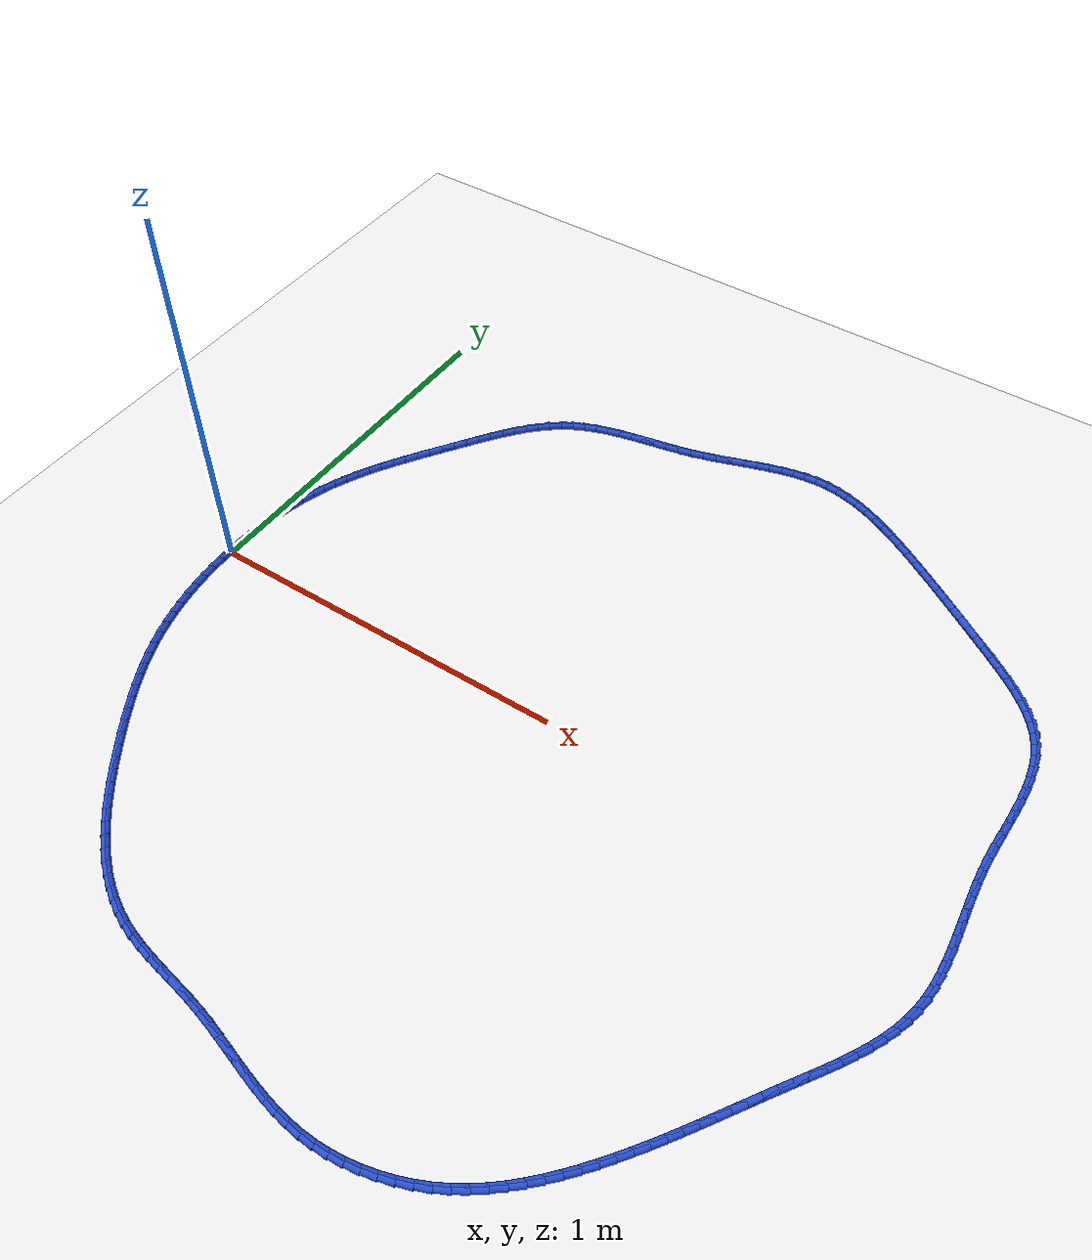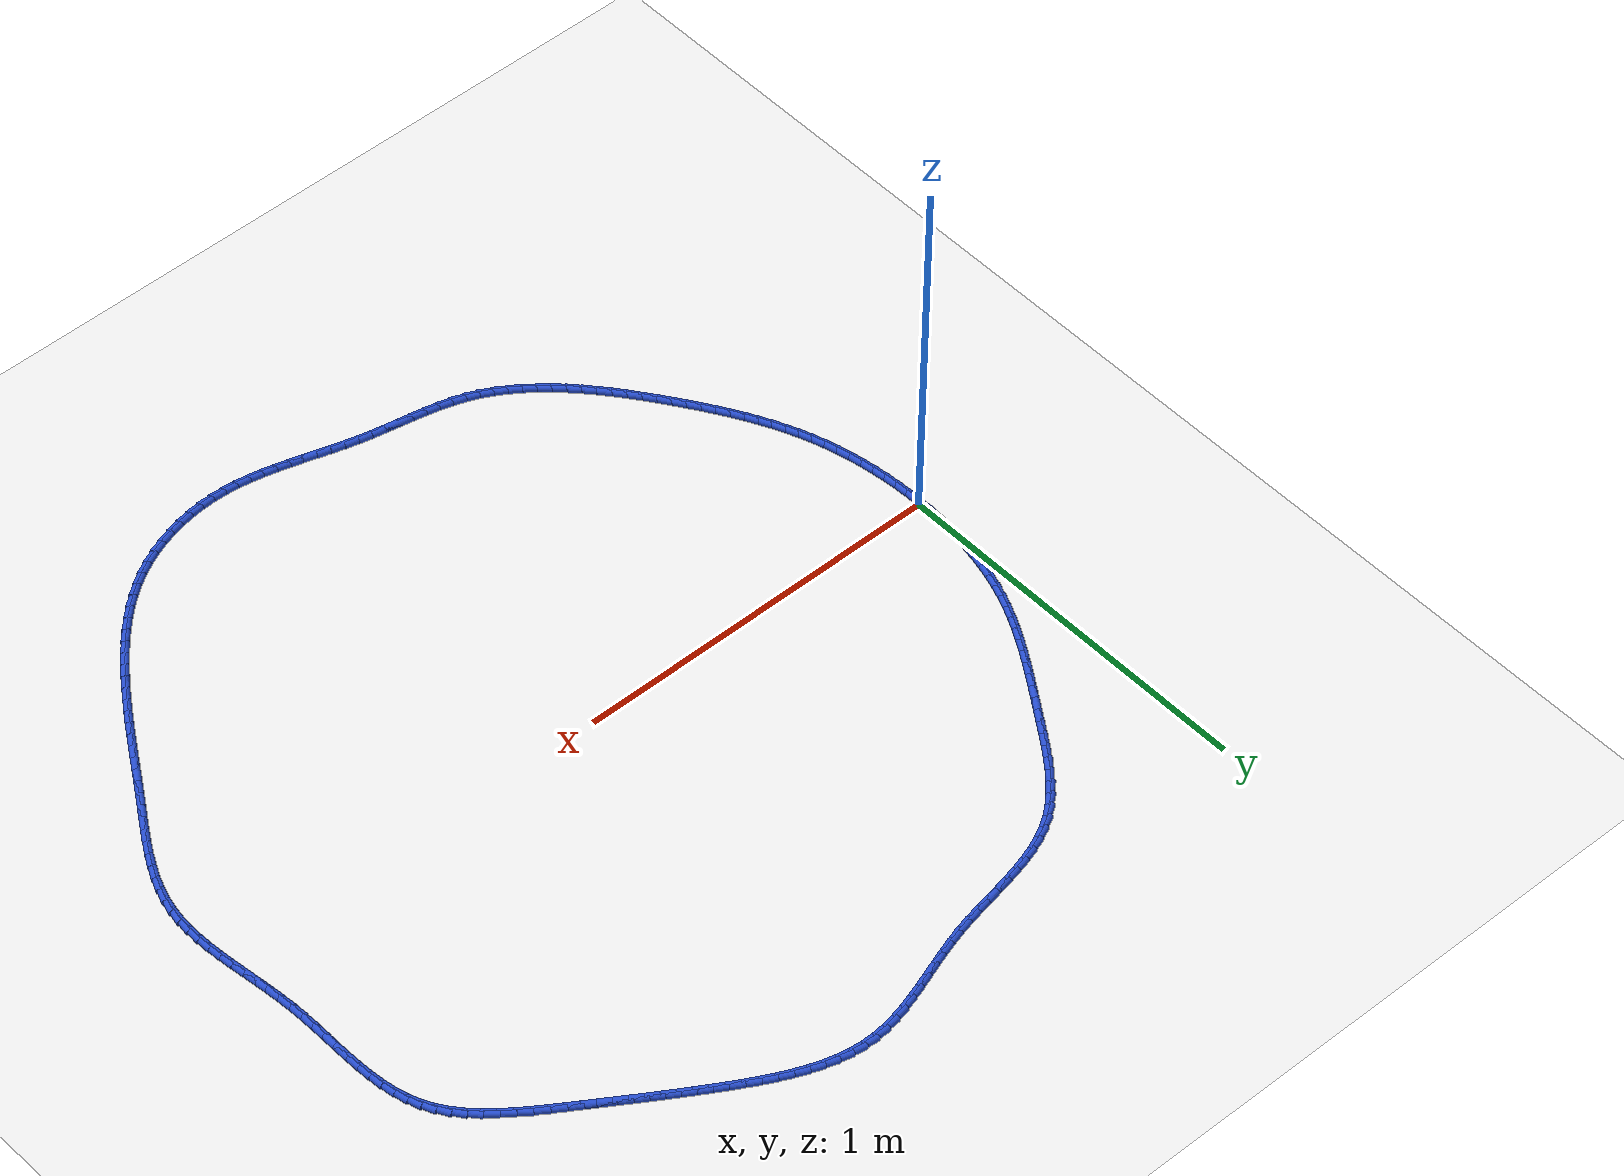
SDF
<sdf version="1.6">
 <world name="default">
  <light name="sun" type="directional">
   <pose>0 0 10 0 -0 0</pose>
   <diffuse>0.8 0.8 0.8 1</diffuse>
   <specular>0.2 0.2 0.2 1</specular>
   <attenuation>
    <range>1000</range>
    <constant>0.9</constant>
    <linear>0.01</linear>
    <quadratic>0.001</quadratic>
   </attenuation>
   <direction>-0.5 0.1 -0.9</direction>
  </light>
  <model name="ground_plane">
   <static>1</static>
   <link name="link">
    <collision name="collision">
     <geometry><plane><normal>0 0 1</normal><size>100 100</size></plane></geometry>
     <surface><friction><ode><mu>100</mu><mu2>50</mu2></ode></friction></surface>
    </collision>
    <visual name="visual">
     <cast_shadows>0</cast_shadows>
     <geometry><plane><normal>0 0 1</normal><size>100 100</size></plane></geometry>
     <material>
      <script><uri>file://media/materials/scripts/gazebo.material</uri><name>Gazebo/WhiteGlow</name></script>
     </material>
    </visual>
   </link>
  </model>
  <gravity>0 0 -9.8</gravity>
  <magnetic_field>6e-06 2.3e-05 -4.2e-05</magnetic_field>
  <atmosphere type="adiabatic"/>
  <physics name="default_physics" default="0" type="ode">
   <max_step_size>0.001</max_step_size>
   <real_time_factor>1</real_time_factor>
   <real_time_update_rate>1000</real_time_update_rate>
  </physics>
  <scene><ambient>0.4 0.4 0.4 1</ambient><background>0.7 0.7 0.7 1</background><shadows>1</shadows></scene>
  <spherical_coordinates>
   <surface_model>EARTH_WGS84</surface_model>
   <latitude_deg>0</latitude_deg>
   <longitude_deg>0</longitude_deg>
   <elevation>0</elevation>
   <heading_deg>0</heading_deg>
  </spherical_coordinates>
  <model name="line">
   <link name="link_0">
    <pose>-5.204170427930421e-18 4.163336342344337e-17 0.01 0 1.57 1.557416992617884</pose>
    <collision name="collision">
     <geometry><cylinder><radius>0.01</radius><length>0.08</length></cylinder></geometry>
    </collision>
    <visual name="visual">
     <material>
      <script><name>Gazebo/Blue</name><uri>file://media/materials/scripts/gazebo.material</uri></script>
     </material>
     <geometry><cylinder><radius>0.01</radius><length>0.08</length></cylinder></geometry>
    </visual>
   </link>
   <link name="link_1">
    <pose>0.0004729191592340061 0.03534487845906107 0.01 0 1.57 1.5244383372521226</pose>
    <collision name="collision">
     <geometry><cylinder><radius>0.01</radius><length>0.08</length></cylinder></geometry>
    </collision>
    <visual name="visual">
     <material>
      <script><name>Gazebo/Blue</name><uri>file://media/materials/scripts/gazebo.material</uri></script>
     </material>
     <geometry><cylinder><radius>0.01</radius><length>0.08</length></cylinder></geometry>
    </visual>
   </link>
   <link name="link_2">
    <pose>0.0021103698437777247 0.07064143764103092 0.01 0 1.57 1.4904017385167414</pose>
    <collision name="collision">
     <geometry><cylinder><radius>0.01</radius><length>0.08</length></cylinder></geometry>
    </collision>
    <visual name="visual">
     <material>
      <script><name>Gazebo/Blue</name><uri>file://media/materials/scripts/gazebo.material</uri></script>
     </material>
     <geometry><cylinder><radius>0.01</radius><length>0.08</length></cylinder></geometry>
    </visual>
   </link>
   <link name="link_3">
    <pose>0.00494411020055783 0.10581336513079691 0.01 0 1.57 1.4551670417448703</pose>
    <collision name="collision">
     <geometry><cylinder><radius>0.01</radius><length>0.08</length></cylinder></geometry>
    </collision>
    <visual name="visual">
     <material>
      <script><name>Gazebo/Blue</name><uri>file://media/materials/scripts/gazebo.material</uri></script>
     </material>
     <geometry><cylinder><radius>0.01</radius><length>0.08</length></cylinder></geometry>
    </visual>
   </link>
   <link name="link_4">
    <pose>0.009005898376501011 0.14078434851324625 0.01 0 1.57 1.4185947935877465</pose>
    <collision name="collision">
     <geometry><cylinder><radius>0.01</radius><length>0.08</length></cylinder></geometry>
    </collision>
    <visual name="visual">
     <material>
      <script><name>Gazebo/Blue</name><uri>file://media/materials/scripts/gazebo.material</uri></script>
     </material>
     <geometry><cylinder><radius>0.01</radius><length>0.08</length></cylinder></geometry>
    </visual>
   </link>
   <link name="link_5">
    <pose>0.014327492518533956 0.17547807537326626 0.01 0 1.57 1.380547403349825</pose>
    <collision name="collision">
     <geometry><cylinder><radius>0.01</radius><length>0.08</length></cylinder></geometry>
    </collision>
    <visual name="visual">
     <material>
      <script><name>Gazebo/Blue</name><uri>file://media/materials/scripts/gazebo.material</uri></script>
     </material>
     <geometry><cylinder><radius>0.01</radius><length>0.08</length></cylinder></geometry>
    </visual>
   </link>
   <link name="link_6">
    <pose>0.020940650773583362 0.20981823329574423 0.01 0 1.57 1.340890981435575</pose>
    <collision name="collision">
     <geometry><cylinder><radius>0.01</radius><length>0.08</length></cylinder></geometry>
    </collision>
    <visual name="visual">
     <material>
      <script><name>Gazebo/Blue</name><uri>file://media/materials/scripts/gazebo.material</uri></script>
     </material>
     <geometry><cylinder><radius>0.01</radius><length>0.08</length></cylinder></geometry>
    </visual>
   </link>
   <link name="link_7">
    <pose>0.028877131288575896 0.24372850986556724 0.01 0 1.57 1.2994979687006996</pose>
    <collision name="collision">
     <geometry><cylinder><radius>0.01</radius><length>0.08</length></cylinder></geometry>
    </collision>
    <visual name="visual">
     <material>
      <script><name>Gazebo/Blue</name><uri>file://media/materials/scripts/gazebo.material</uri></script>
     </material>
     <geometry><cylinder><radius>0.01</radius><length>0.08</length></cylinder></geometry>
    </visual>
   </link>
   <link name="link_8">
    <pose>0.03816869221043826 0.2771325926676227 0.01 0 1.57 1.2562506655497028</pose>
    <collision name="collision">
     <geometry><cylinder><radius>0.01</radius><length>0.08</length></cylinder></geometry>
    </collision>
    <visual name="visual">
     <material>
      <script><name>Gazebo/Blue</name><uri>file://media/materials/scripts/gazebo.material</uri></script>
     </material>
     <geometry><cylinder><radius>0.01</radius><length>0.08</length></cylinder></geometry>
    </visual>
   </link>
   <link name="link_9">
    <pose>0.04884709168609716 0.309954169286798 0.01 0 1.57 1.2112063816526473</pose>
    <collision name="collision">
     <geometry><cylinder><radius>0.01</radius><length>0.08</length></cylinder></geometry>
    </collision>
    <visual name="visual">
     <material>
      <script><name>Gazebo/Blue</name><uri>file://media/materials/scripts/gazebo.material</uri></script>
     </material>
     <geometry><cylinder><radius>0.01</radius><length>0.08</length></cylinder></geometry>
    </visual>
   </link>
   <link name="link_10">
    <pose>0.060939858221996795 0.34212136266955595 0.01 0 1.57 1.167394309123897</pose>
    <collision name="collision">
     <geometry><cylinder><radius>0.01</radius><length>0.08</length></cylinder></geometry>
    </collision>
    <visual name="visual">
     <material>
      <script><name>Gazebo/Blue</name><uri>file://media/materials/scripts/gazebo.material</uri></script>
     </material>
     <geometry><cylinder><radius>0.01</radius><length>0.08</length></cylinder></geometry>
    </visual>
   </link>
   <link name="link_11">
    <pose>0.07439481141822145 0.37364588154748485 0.01 0 1.57 1.127766253802123</pose>
    <collision name="collision">
     <geometry><cylinder><radius>0.01</radius><length>0.08</length></cylinder></geometry>
    </collision>
    <visual name="visual">
     <material>
      <script><name>Gazebo/Blue</name><uri>file://media/materials/scripts/gazebo.material</uri></script>
     </material>
     <geometry><cylinder><radius>0.01</radius><length>0.08</length></cylinder></geometry>
    </visual>
   </link>
   <link name="link_12">
    <pose>0.08908875183017924 0.4046139079184511 0.01 0 1.57 1.0926438489299295</pose>
    <collision name="collision">
     <geometry><cylinder><radius>0.01</radius><length>0.08</length></cylinder></geometry>
    </collision>
    <visual name="visual">
     <material>
      <script><name>Gazebo/Blue</name><uri>file://media/materials/scripts/gazebo.material</uri></script>
     </material>
     <geometry><cylinder><radius>0.01</radius><length>0.08</length></cylinder></geometry>
    </visual>
   </link>
   <link name="link_13">
    <pose>0.10489599560796861 0.4351142290220418 0.01 0 1.57 1.0621579611416831</pose>
    <collision name="collision">
     <geometry><cylinder><radius>0.01</radius><length>0.08</length></cylinder></geometry>
    </collision>
    <visual name="visual">
     <material>
      <script><name>Gazebo/Blue</name><uri>file://media/materials/scripts/gazebo.material</uri></script>
     </material>
     <geometry><cylinder><radius>0.01</radius><length>0.08</length></cylinder></geometry>
    </visual>
   </link>
   <link name="link_14">
    <pose>0.12169085890168807 0.46523563209784374 0.01 0 1.57 1.0363622172110625</pose>
    <collision name="collision">
     <geometry><cylinder><radius>0.01</radius><length>0.08</length></cylinder></geometry>
    </collision>
    <visual name="visual">
     <material>
      <script><name>Gazebo/Blue</name><uri>file://media/materials/scripts/gazebo.material</uri></script>
     </material>
     <geometry><cylinder><radius>0.01</radius><length>0.08</length></cylinder></geometry>
    </visual>
   </link>
   <link name="link_15">
    <pose>0.1393476578614362 0.49506690438544454 0.01 0 1.57 1.015252391539737</pose>
    <collision name="collision">
     <geometry><cylinder><radius>0.01</radius><length>0.08</length></cylinder></geometry>
    </collision>
    <visual name="visual">
     <material>
      <script><name>Gazebo/Blue</name><uri>file://media/materials/scripts/gazebo.material</uri></script>
     </material>
     <geometry><cylinder><radius>0.01</radius><length>0.08</length></cylinder></geometry>
    </visual>
   </link>
   <link name="link_16">
    <pose>0.15774070863731146 0.5246968331244308 0.01 0 1.57 0.9987839765120892</pose>
    <collision name="collision">
     <geometry><cylinder><radius>0.01</radius><length>0.08</length></cylinder></geometry>
    </collision>
    <visual name="visual">
     <material>
      <script><name>Gazebo/Blue</name><uri>file://media/materials/scripts/gazebo.material</uri></script>
     </material>
     <geometry><cylinder><radius>0.01</radius><length>0.08</length></cylinder></geometry>
    </visual>
   </link>
   <link name="link_17">
    <pose>0.17674432737941245 0.5542142055543904 0.01 0 1.57 0.9868868047825836</pose>
    <collision name="collision">
     <geometry><cylinder><radius>0.01</radius><length>0.08</length></cylinder></geometry>
    </collision>
    <visual name="visual">
     <material>
      <script><name>Gazebo/Blue</name><uri>file://media/materials/scripts/gazebo.material</uri></script>
     </material>
     <geometry><cylinder><radius>0.01</radius><length>0.08</length></cylinder></geometry>
    </visual>
   </link>
   <link name="link_18">
    <pose>0.19623283023783752 0.5837078089149095 0.01 0 1.57 0.9794762773099808</pose>
    <collision name="collision">
     <geometry><cylinder><radius>0.01</radius><length>0.08</length></cylinder></geometry>
    </collision>
    <visual name="visual">
     <material>
      <script><name>Gazebo/Blue</name><uri>file://media/materials/scripts/gazebo.material</uri></script>
     </material>
     <geometry><cylinder><radius>0.01</radius><length>0.08</length></cylinder></geometry>
    </visual>
   </link>
   <link name="link_19">
    <pose>0.21608053336268526 0.6132664304455759 0.01 0 1.57 0.9764611975546676</pose>
    <collision name="collision">
     <geometry><cylinder><radius>0.01</radius><length>0.08</length></cylinder></geometry>
    </collision>
    <visual name="visual">
     <material>
      <script><name>Gazebo/Blue</name><uri>file://media/materials/scripts/gazebo.material</uri></script>
     </material>
     <geometry><cylinder><radius>0.01</radius><length>0.08</length></cylinder></geometry>
    </visual>
   </link>
   <link name="link_20">
    <pose>0.2361617529040543 0.6429788573859767 0.01 0 1.57 0.9772397947336325</pose>
    <collision name="collision">
     <geometry><cylinder><radius>0.01</radius><length>0.08</length></cylinder></geometry>
    </collision>
    <visual name="visual">
     <material>
      <script><name>Gazebo/Blue</name><uri>file://media/materials/scripts/gazebo.material</uri></script>
     </material>
     <geometry><cylinder><radius>0.01</radius><length>0.08</length></cylinder></geometry>
    </visual>
   </link>
   <link name="link_21">
    <pose>0.25636192251204426 0.6729175021427375 0.01 0 1.57 0.9742280329714942</pose>
    <collision name="collision">
     <geometry><cylinder><radius>0.01</radius><length>0.08</length></cylinder></geometry>
    </collision>
    <visual name="visual">
     <material>
      <script><name>Gazebo/Blue</name><uri>file://media/materials/scripts/gazebo.material</uri></script>
     </material>
     <geometry><cylinder><radius>0.01</radius><length>0.08</length></cylinder></geometry>
    </visual>
   </link>
   <link name="link_22">
    <pose>0.2767314066519709 0.702911852494736 0.01 0 1.57 0.9616569370458535</pose>
    <collision name="collision">
     <geometry><cylinder><radius>0.01</radius><length>0.08</length></cylinder></geometry>
    </collision>
    <visual name="visual">
     <material>
      <script><name>Gazebo/Blue</name><uri>file://media/materials/scripts/gazebo.material</uri></script>
     </material>
     <geometry><cylinder><radius>0.01</radius><length>0.08</length></cylinder></geometry>
    </visual>
   </link>
   <link name="link_23">
    <pose>0.29744681153537267 0.7326054562607075 0.01 0 1.57 0.9391406261261201</pose>
    <collision name="collision">
     <geometry><cylinder><radius>0.01</radius><length>0.08</length></cylinder></geometry>
    </collision>
    <visual name="visual">
     <material>
      <script><name>Gazebo/Blue</name><uri>file://media/materials/scripts/gazebo.material</uri></script>
     </material>
     <geometry><cylinder><radius>0.01</radius><length>0.08</length></cylinder></geometry>
    </visual>
   </link>
   <link name="link_24">
    <pose>0.3186879493006809 0.7616371392879588 0.01 0 1.57 0.9061544220299828</pose>
    <collision name="collision">
     <geometry><cylinder><radius>0.01</radius><length>0.08</length></cylinder></geometry>
    </collision>
    <visual name="visual">
     <material>
      <script><name>Gazebo/Blue</name><uri>file://media/materials/scripts/gazebo.material</uri></script>
     </material>
     <geometry><cylinder><radius>0.01</radius><length>0.08</length></cylinder></geometry>
    </visual>
   </link>
   <link name="link_25">
    <pose>0.34063463208632705 0.7896457274237966 0.01 0 1.57 0.861927710346363</pose>
    <collision name="collision">
     <geometry><cylinder><radius>0.01</radius><length>0.08</length></cylinder></geometry>
    </collision>
    <visual name="visual">
     <material>
      <script><name>Gazebo/Blue</name><uri>file://media/materials/scripts/gazebo.material</uri></script>
     </material>
     <geometry><cylinder><radius>0.01</radius><length>0.08</length></cylinder></geometry>
    </visual>
   </link>
   <link name="link_26">
    <pose>0.3634666720307429 0.8162700465155283 0.01 0 1.57 0.8055214295372826</pose>
    <collision name="collision">
     <geometry><cylinder><radius>0.01</radius><length>0.08</length></cylinder></geometry>
    </collision>
    <visual name="visual">
     <material>
      <script><name>Gazebo/Blue</name><uri>file://media/materials/scripts/gazebo.material</uri></script>
     </material>
     <geometry><cylinder><radius>0.01</radius><length>0.08</length></cylinder></geometry>
    </visual>
   </link>
   <link name="link_27">
    <pose>0.38736388127235977 0.8411489224104604 0.01 0 1.57 0.7359766976180857</pose>
    <collision name="collision">
     <geometry><cylinder><radius>0.01</radius><length>0.08</length></cylinder></geometry>
    </collision>
    <visual name="visual">
     <material>
      <script><name>Gazebo/Blue</name><uri>file://media/materials/scripts/gazebo.material</uri></script>
     </material>
     <geometry><cylinder><radius>0.01</radius><length>0.08</length></cylinder></geometry>
    </visual>
   </link>
   <link name="link_28">
    <pose>0.41250607194960914 0.8639211809558998 0.01 0 1.57 0.6525743331727882</pose>
    <collision name="collision">
     <geometry><cylinder><radius>0.01</radius><length>0.08</length></cylinder></geometry>
    </collision>
    <visual name="visual">
     <material>
      <script><name>Gazebo/Blue</name><uri>file://media/materials/scripts/gazebo.material</uri></script>
     </material>
     <geometry><cylinder><radius>0.01</radius><length>0.08</length></cylinder></geometry>
    </visual>
   </link>
   <link name="link_29">
    <pose>0.4390730562009228 0.8842256479991529 0.01 0 1.57 0.5557082397295324</pose>
    <collision name="collision">
     <geometry><cylinder><radius>0.01</radius><length>0.08</length></cylinder></geometry>
    </collision>
    <visual name="visual">
     <material>
      <script><name>Gazebo/Blue</name><uri>file://media/materials/scripts/gazebo.material</uri></script>
     </material>
     <geometry><cylinder><radius>0.01</radius><length>0.08</length></cylinder></geometry>
    </visual>
   </link>
   <link name="link_30">
    <pose>0.46723772512531947 0.9017155367052778 0.01 0 1.57 0.45861255509707066</pose>
    <collision name="collision">
     <geometry><cylinder><radius>0.01</radius><length>0.08</length></cylinder></geometry>
    </collision>
    <visual name="visual">
     <material>
      <script><name>Gazebo/Blue</name><uri>file://media/materials/scripts/gazebo.material</uri></script>
     </material>
     <geometry><cylinder><radius>0.01</radius><length>0.08</length></cylinder></geometry>
    </visual>
   </link>
   <link name="link_31">
    <pose>0.49699759059148263 0.9164086350615877 0.01 0 1.57 0.37583269068381064</pose>
    <collision name="collision">
     <geometry><cylinder><radius>0.01</radius><length>0.08</length></cylinder></geometry>
    </collision>
    <visual name="visual">
     <material>
      <script><name>Gazebo/Blue</name><uri>file://media/materials/scripts/gazebo.material</uri></script>
     </material>
     <geometry><cylinder><radius>0.01</radius><length>0.08</length></cylinder></geometry>
    </visual>
   </link>
   <link name="link_32">
    <pose>0.5281652861289297 0.9287070524343359 0.01 0 1.57 0.3086603809641968</pose>
    <collision name="collision">
     <geometry><cylinder><radius>0.01</radius><length>0.08</length></cylinder></geometry>
    </collision>
    <visual name="visual">
     <material>
      <script><name>Gazebo/Blue</name><uri>file://media/materials/scripts/gazebo.material</uri></script>
     </material>
     <geometry><cylinder><radius>0.01</radius><length>0.08</length></cylinder></geometry>
    </visual>
   </link>
   <link name="link_33">
    <pose>0.5605446227488382 0.9390312382637411 0.01 0 1.57 0.256827995575996</pose>
    <collision name="collision">
     <geometry><cylinder><radius>0.01</radius><length>0.08</length></cylinder></geometry>
    </collision>
    <visual name="visual">
     <material>
      <script><name>Gazebo/Blue</name><uri>file://media/materials/scripts/gazebo.material</uri></script>
     </material>
     <geometry><cylinder><radius>0.01</radius><length>0.08</length></cylinder></geometry>
    </visual>
   </link>
   <link name="link_34">
    <pose>0.5939394114623849 0.9478016419900197 0.01 0 1.57 0.21961429014175182</pose>
    <collision name="collision">
     <geometry><cylinder><radius>0.01</radius><length>0.08</length></cylinder></geometry>
    </collision>
    <visual name="visual">
     <material>
      <script><name>Gazebo/Blue</name><uri>file://media/materials/scripts/gazebo.material</uri></script>
     </material>
     <geometry><cylinder><radius>0.01</radius><length>0.08</length></cylinder></geometry>
    </visual>
   </link>
   <link name="link_35">
    <pose>0.6281534632807472 0.9554387130533899 0.01 0 1.57 0.19620188282423384</pose>
    <collision name="collision">
     <geometry><cylinder><radius>0.01</radius><length>0.08</length></cylinder></geometry>
    </collision>
    <visual name="visual">
     <material>
      <script><name>Gazebo/Blue</name><uri>file://media/materials/scripts/gazebo.material</uri></script>
     </material>
     <geometry><cylinder><radius>0.01</radius><length>0.08</length></cylinder></geometry>
    </visual>
   </link>
   <link name="link_36">
    <pose>0.6629905892151018 0.9623629008940683 0.01 0 1.57 0.18588898954116423</pose>
    <collision name="collision">
     <geometry><cylinder><radius>0.01</radius><length>0.08</length></cylinder></geometry>
    </collision>
    <visual name="visual">
     <material>
      <script><name>Gazebo/Blue</name><uri>file://media/materials/scripts/gazebo.material</uri></script>
     </material>
     <geometry><cylinder><radius>0.01</radius><length>0.08</length></cylinder></geometry>
    </visual>
   </link>
   <link name="link_37">
    <pose>0.698254600276626 0.9689946549522728 0.01 0 1.57 0.18819086844707827</pose>
    <collision name="collision">
     <geometry><cylinder><radius>0.01</radius><length>0.08</length></cylinder></geometry>
    </collision>
    <visual name="visual">
     <material>
      <script><name>Gazebo/Blue</name><uri>file://media/materials/scripts/gazebo.material</uri></script>
     </material>
     <geometry><cylinder><radius>0.01</radius><length>0.08</length></cylinder></geometry>
    </visual>
   </link>
   <link name="link_38">
    <pose>0.7337493074764967 0.9757544246682206 0.01 0 1.57 0.20286690918502082</pose>
    <collision name="collision">
     <geometry><cylinder><radius>0.01</radius><length>0.08</length></cylinder></geometry>
    </collision>
    <visual name="visual">
     <material>
      <script><name>Gazebo/Blue</name><uri>file://media/materials/scripts/gazebo.material</uri></script>
     </material>
     <geometry><cylinder><radius>0.01</radius><length>0.08</length></cylinder></geometry>
    </visual>
   </link>
   <link name="link_39">
    <pose>0.7692785218258913 0.9830626594821292 0.01 0 1.57 0.22989482461553473</pose>
    <collision name="collision">
     <geometry><cylinder><radius>0.01</radius><length>0.08</length></cylinder></geometry>
    </collision>
    <visual name="visual">
     <material>
      <script><name>Gazebo/Blue</name><uri>file://media/materials/scripts/gazebo.material</uri></script>
     </material>
     <geometry><cylinder><radius>0.01</radius><length>0.08</length></cylinder></geometry>
    </visual>
   </link>
   <link name="link_40">
    <pose>0.8046460543359863 0.9913398088342159 0.01 0 1.57 0.26764180865991144</pose>
    <collision name="collision">
     <geometry><cylinder><radius>0.01</radius><length>0.08</length></cylinder></geometry>
    </collision>
    <visual name="visual">
     <material>
      <script><name>Gazebo/Blue</name><uri>file://media/materials/scripts/gazebo.material</uri></script>
     </material>
     <geometry><cylinder><radius>0.01</radius><length>0.08</length></cylinder></geometry>
    </visual>
   </link>
   <link name="link_41">
    <pose>0.8396722784553271 1.0009447339837694 0.01 0 1.57 0.3007225226367122</pose>
    <collision name="collision">
     <geometry><cylinder><radius>0.01</radius><length>0.08</length></cylinder></geometry>
    </collision>
    <visual name="visual">
     <material>
      <script><name>Gazebo/Blue</name><uri>file://media/materials/scripts/gazebo.material</uri></script>
     </material>
     <geometry><cylinder><radius>0.01</radius><length>0.08</length></cylinder></geometry>
    </visual>
   </link>
   <link name="link_42">
    <pose>0.8743241426384506 1.011691250325863 0.01 0 1.57 0.3211499340487126</pose>
    <collision name="collision">
     <geometry><cylinder><radius>0.01</radius><length>0.08</length></cylinder></geometry>
    </collision>
    <visual name="visual">
     <material>
      <script><name>Gazebo/Blue</name><uri>file://media/materials/scripts/gazebo.material</uri></script>
     </material>
     <geometry><cylinder><radius>0.01</radius><length>0.08</length></cylinder></geometry>
    </visual>
   </link>
   <link name="link_43">
    <pose>0.9086451043059034 1.0231086711658965 0.01 0 1.57 0.328885016787121</pose>
    <collision name="collision">
     <geometry><cylinder><radius>0.01</radius><length>0.08</length></cylinder></geometry>
    </collision>
    <visual name="visual">
     <material>
      <script><name>Gazebo/Blue</name><uri>file://media/materials/scripts/gazebo.material</uri></script>
     </material>
     <geometry><cylinder><radius>0.01</radius><length>0.08</length></cylinder></geometry>
    </visual>
   </link>
   <link name="link_44">
    <pose>0.9426792848383097 1.034723840843351 0.01 0 1.57 0.3237713044182833</pose>
    <collision name="collision">
     <geometry><cylinder><radius>0.01</radius><length>0.08</length></cylinder></geometry>
    </collision>
    <visual name="visual">
     <material>
      <script><name>Gazebo/Blue</name><uri>file://media/materials/scripts/gazebo.material</uri></script>
     </material>
     <geometry><cylinder><radius>0.01</radius><length>0.08</length></cylinder></geometry>
    </visual>
   </link>
   <link name="link_45">
    <pose>0.9764708056162924 1.046063603697708 0.01 0 1.57 0.3054156611825449</pose>
    <collision name="collision">
     <geometry><cylinder><radius>0.01</radius><length>0.08</length></cylinder></geometry>
    </collision>
    <visual name="visual">
     <material>
      <script><name>Gazebo/Blue</name><uri>file://media/materials/scripts/gazebo.material</uri></script>
     </material>
     <geometry><cylinder><radius>0.01</radius><length>0.08</length></cylinder></geometry>
    </visual>
   </link>
   <link name="link_46">
    <pose>1.0100637880204768 1.0566548040684494 0.01 0 1.57 0.2731940479832857</pose>
    <collision name="collision">
     <geometry><cylinder><radius>0.01</radius><length>0.08</length></cylinder></geometry>
    </collision>
    <visual name="visual">
     <material>
      <script><name>Gazebo/Blue</name><uri>file://media/materials/scripts/gazebo.material</uri></script>
     </material>
     <geometry><cylinder><radius>0.01</radius><length>0.08</length></cylinder></geometry>
    </visual>
   </link>
   <link name="link_47">
    <pose>1.043502353431486 1.0660242862950562 0.01 0 1.57 0.2263278772536575</pose>
    <collision name="collision">
     <geometry><cylinder><radius>0.01</radius><length>0.08</length></cylinder></geometry>
    </collision>
    <visual name="visual">
     <material>
      <script><name>Gazebo/Blue</name><uri>file://media/materials/scripts/gazebo.material</uri></script>
     </material>
     <geometry><cylinder><radius>0.01</radius><length>0.08</length></cylinder></geometry>
    </visual>
   </link>
   <link name="link_48">
    <pose>1.0768306232299443 1.073698894717011 0.01 0 1.57 0.16406313685221804</pose>
    <collision name="collision">
     <geometry><cylinder><radius>0.01</radius><length>0.08</length></cylinder></geometry>
    </collision>
    <visual name="visual">
     <material>
      <script><name>Gazebo/Blue</name><uri>file://media/materials/scripts/gazebo.material</uri></script>
     </material>
     <geometry><cylinder><radius>0.01</radius><length>0.08</length></cylinder></geometry>
    </visual>
   </link>
   <link name="link_49">
    <pose>1.1100927187964746 1.079205473673794 0.01 0 1.57 0.08599049591824336</pose>
    <collision name="collision">
     <geometry><cylinder><radius>0.01</radius><length>0.08</length></cylinder></geometry>
    </collision>
    <visual name="visual">
     <material>
      <script><name>Gazebo/Blue</name><uri>file://media/materials/scripts/gazebo.material</uri></script>
     </material>
     <geometry><cylinder><radius>0.01</radius><length>0.08</length></cylinder></geometry>
    </visual>
   </link>
   <link name="link_50">
    <pose>1.143332761511702 1.0820708675048876 0.01 0 1.57 -0.007457082796193526</pose>
    <collision name="collision">
     <geometry><cylinder><radius>0.01</radius><length>0.08</length></cylinder></geometry>
    </collision>
    <visual name="visual">
     <material>
      <script><name>Gazebo/Blue</name><uri>file://media/materials/scripts/gazebo.material</uri></script>
     </material>
     <geometry><cylinder><radius>0.01</radius><length>0.08</length></cylinder></geometry>
    </visual>
   </link>
   <link name="link_51">
    <pose>1.1765947472734426 1.0818228255253663 0.01 0 1.57 -0.10786044686578283</pose>
    <collision name="collision">
     <geometry><cylinder><radius>0.01</radius><length>0.08</length></cylinder></geometry>
    </collision>
    <visual name="visual">
     <material>
      <script><name>Gazebo/Blue</name><uri>file://media/materials/scripts/gazebo.material</uri></script>
     </material>
     <geometry><cylinder><radius>0.01</radius><length>0.08</length></cylinder></geometry>
    </visual>
   </link>
   <link name="link_52">
    <pose>1.2098910041019675 1.0782174841642487 0.01 0 1.57 -0.19808350186419435</pose>
    <collision name="collision">
     <geometry><cylinder><radius>0.01</radius><length>0.08</length></cylinder></geometry>
    </collision>
    <visual name="visual">
     <material>
      <script><name>Gazebo/Blue</name><uri>file://media/materials/scripts/gazebo.material</uri></script>
     </material>
     <geometry><cylinder><radius>0.01</radius><length>0.08</length></cylinder></geometry>
    </visual>
   </link>
   <link name="link_53">
    <pose>1.2431605384846391 1.071539770997571 0.01 0 1.57 -0.2758722713030723</pose>
    <collision name="collision">
     <geometry><cylinder><radius>0.01</radius><length>0.08</length></cylinder></geometry>
    </collision>
    <visual name="visual">
     <material>
      <script><name>Gazebo/Blue</name><uri>file://media/materials/scripts/gazebo.material</uri></script>
     </material>
     <geometry><cylinder><radius>0.01</radius><length>0.08</length></cylinder></geometry>
    </visual>
   </link>
   <link name="link_54">
    <pose>1.2763320091883412 1.062149240832479 0.01 0 1.57 -0.34187705970006044</pose>
    <collision name="collision">
     <geometry><cylinder><radius>0.01</radius><length>0.08</length></cylinder></geometry>
    </collision>
    <visual name="visual">
     <material>
      <script><name>Gazebo/Blue</name><uri>file://media/materials/scripts/gazebo.material</uri></script>
     </material>
     <geometry><cylinder><radius>0.01</radius><length>0.08</length></cylinder></geometry>
    </visual>
   </link>
   <link name="link_55">
    <pose>1.3093340749799565 1.0504054484761185 0.01 0 1.57 -0.39705041844144895</pose>
    <collision name="collision">
     <geometry><cylinder><radius>0.01</radius><length>0.08</length></cylinder></geometry>
    </collision>
    <visual name="visual">
     <material>
      <script><name>Gazebo/Blue</name><uri>file://media/materials/scripts/gazebo.material</uri></script>
     </material>
     <geometry><cylinder><radius>0.01</radius><length>0.08</length></cylinder></geometry>
    </visual>
   </link>
   <link name="link_56">
    <pose>1.3420953946263674 1.0366679487356352 0.01 0 1.57 -0.44239847002535004</pose>
    <collision name="collision">
     <geometry><cylinder><radius>0.01</radius><length>0.08</length></cylinder></geometry>
    </collision>
    <visual name="visual">
     <material>
      <script><name>Gazebo/Blue</name><uri>file://media/materials/scripts/gazebo.material</uri></script>
     </material>
     <geometry><cylinder><radius>0.01</radius><length>0.08</length></cylinder></geometry>
    </visual>
   </link>
   <link name="link_57">
    <pose>1.3745446268944579 1.0212962964181744 0.01 0 1.57 -0.4788324909944102</pose>
    <collision name="collision">
     <geometry><cylinder><radius>0.01</radius><length>0.08</length></cylinder></geometry>
    </collision>
    <visual name="visual">
     <material>
      <script><name>Gazebo/Blue</name><uri>file://media/materials/scripts/gazebo.material</uri></script>
     </material>
     <geometry><cylinder><radius>0.01</radius><length>0.08</length></cylinder></geometry>
    </visual>
   </link>
   <link name="link_58">
    <pose>1.4066104305511111 1.0046500463308827 0.01 0 1.57 -0.50708901861214</pose>
    <collision name="collision">
     <geometry><cylinder><radius>0.01</radius><length>0.08</length></cylinder></geometry>
    </collision>
    <visual name="visual">
     <material>
      <script><name>Gazebo/Blue</name><uri>file://media/materials/scripts/gazebo.material</uri></script>
     </material>
     <geometry><cylinder><radius>0.01</radius><length>0.08</length></cylinder></geometry>
    </visual>
   </link>
   <link name="link_59">
    <pose>1.438221464363209 0.9870887532809057 0.01 0 1.57 -0.5276881528092047</pose>
    <collision name="collision">
     <geometry><cylinder><radius>0.01</radius><length>0.08</length></cylinder></geometry>
    </collision>
    <visual name="visual">
     <material>
      <script><name>Gazebo/Blue</name><uri>file://media/materials/scripts/gazebo.material</uri></script>
     </material>
     <geometry><cylinder><radius>0.01</radius><length>0.08</length></cylinder></geometry>
    </visual>
   </link>
   <link name="link_60">
    <pose>1.4693063870976357 0.9689719720753888 0.01 0 1.57 -0.5409907027923895</pose>
    <collision name="collision">
     <geometry><cylinder><radius>0.01</radius><length>0.08</length></cylinder></geometry>
    </collision>
    <visual name="visual">
     <material>
      <script><name>Gazebo/Blue</name><uri>file://media/materials/scripts/gazebo.material</uri></script>
     </material>
     <geometry><cylinder><radius>0.01</radius><length>0.08</length></cylinder></geometry>
    </visual>
   </link>
   <link name="link_61">
    <pose>1.4997963910785421 0.9506542758485372 0.01 0 1.57 -0.5498641520774867</pose>
    <collision name="collision">
     <geometry><cylinder><radius>0.01</radius><length>0.08</length></cylinder></geometry>
    </collision>
    <visual name="visual">
     <material>
      <script><name>Gazebo/Blue</name><uri>file://media/materials/scripts/gazebo.material</uri></script>
     </material>
     <geometry><cylinder><radius>0.01</radius><length>0.08</length></cylinder></geometry>
    </visual>
   </link>
   <link name="link_62">
    <pose>1.5297091451712355 0.9323202009840712 0.01 0 1.57 -0.5576747471915224</pose>
    <collision name="collision">
     <geometry><cylinder><radius>0.01</radius><length>0.08</length></cylinder></geometry>
    </collision>
    <visual name="visual">
     <material>
      <script><name>Gazebo/Blue</name><uri>file://media/materials/scripts/gazebo.material</uri></script>
     </material>
     <geometry><cylinder><radius>0.01</radius><length>0.08</length></cylinder></geometry>
    </visual>
   </link>
   <link name="link_63">
    <pose>1.5591681589802753 0.9139461717565712 0.01 0 1.57 -0.5645188190107896</pose>
    <collision name="collision">
     <geometry><cylinder><radius>0.01</radius><length>0.08</length></cylinder></geometry>
    </collision>
    <visual name="visual">
     <material>
      <script><name>Gazebo/Blue</name><uri>file://media/materials/scripts/gazebo.material</uri></script>
     </material>
     <geometry><cylinder><radius>0.01</radius><length>0.08</length></cylinder></geometry>
    </visual>
   </link>
   <link name="link_64">
    <pose>1.5883033981431234 0.8954959180978344 0.01 0 1.57 -0.5702987687697424</pose>
    <collision name="collision">
     <geometry><cylinder><radius>0.01</radius><length>0.08</length></cylinder></geometry>
    </collision>
    <visual name="visual">
     <material>
      <script><name>Gazebo/Blue</name><uri>file://media/materials/scripts/gazebo.material</uri></script>
     </material>
     <geometry><cylinder><radius>0.01</radius><length>0.08</length></cylinder></geometry>
    </visual>
   </link>
   <link name="link_65">
    <pose>1.6172448282972431 0.8769331699396603 0.01 0 1.57 -0.5749395836031098</pose>
    <collision name="collision">
     <geometry><cylinder><radius>0.01</radius><length>0.08</length></cylinder></geometry>
    </collision>
    <visual name="visual">
     <material>
      <script><name>Gazebo/Blue</name><uri>file://media/materials/scripts/gazebo.material</uri></script>
     </material>
     <geometry><cylinder><radius>0.01</radius><length>0.08</length></cylinder></geometry>
    </visual>
   </link>
   <link name="link_66">
    <pose>1.6461224150800964 0.8582216572138475 0.01 0 1.57 -0.5783917982291823</pose>
    <collision name="collision">
     <geometry><cylinder><radius>0.01</radius><length>0.08</length></cylinder></geometry>
    </collision>
    <visual name="visual">
     <material>
      <script><name>Gazebo/Blue</name><uri>file://media/materials/scripts/gazebo.material</uri></script>
     </material>
     <geometry><cylinder><radius>0.01</radius><length>0.08</length></cylinder></geometry>
    </visual>
   </link>
   <link name="link_67">
    <pose>1.6750661241291458 0.8393251098521932 0.01 0 1.57 -0.5806330580157035</pose>
    <collision name="collision">
     <geometry><cylinder><radius>0.01</radius><length>0.08</length></cylinder></geometry>
    </collision>
    <visual name="visual">
     <material>
      <script><name>Gazebo/Blue</name><uri>file://media/materials/scripts/gazebo.material</uri></script>
     </material>
     <geometry><cylinder><radius>0.01</radius><length>0.08</length></cylinder></geometry>
    </visual>
   </link>
   <link name="link_68">
    <pose>1.704205921081854 0.8202072577864971 0.01 0 1.57 -0.5816681969115279</pose>
    <collision name="collision">
     <geometry><cylinder><radius>0.01</radius><length>0.08</length></cylinder></geometry>
    </collision>
    <visual name="visual">
     <material>
      <script><name>Gazebo/Blue</name><uri>file://media/materials/scripts/gazebo.material</uri></script>
     </material>
     <geometry><cylinder><radius>0.01</radius><length>0.08</length></cylinder></geometry>
    </visual>
   </link>
   <link name="link_69">
    <pose>1.7336717715756842 0.8008318309485569 0.01 0 1.57 -0.5816729274176559</pose>
    <collision name="collision">
     <geometry><cylinder><radius>0.01</radius><length>0.08</length></cylinder></geometry>
    </collision>
    <visual name="visual">
     <material>
      <script><name>Gazebo/Blue</name><uri>file://media/materials/scripts/gazebo.material</uri></script>
     </material>
     <geometry><cylinder><radius>0.01</radius><length>0.08</length></cylinder></geometry>
    </visual>
   </link>
   <link name="link_70">
    <pose>1.7635863780623269 0.781161119520486 0.01 0 1.57 -0.5858528518757431</pose>
    <collision name="collision">
     <geometry><cylinder><radius>0.01</radius><length>0.08</length></cylinder></geometry>
    </collision>
    <visual name="visual">
     <material>
      <script><name>Gazebo/Blue</name><uri>file://media/materials/scripts/gazebo.material</uri></script>
     </material>
     <geometry><cylinder><radius>0.01</radius><length>0.08</length></cylinder></geometry>
    </visual>
   </link>
   <link name="link_71">
    <pose>1.7938104219180102 0.761105474387644 0.01 0 1.57 -0.6006071684975742</pose>
    <collision name="collision">
     <geometry><cylinder><radius>0.01</radius><length>0.08</length></cylinder></geometry>
    </collision>
    <visual name="visual">
     <material>
      <script><name>Gazebo/Blue</name><uri>file://media/materials/scripts/gazebo.material</uri></script>
     </material>
     <geometry><cylinder><radius>0.01</radius><length>0.08</length></cylinder></geometry>
    </visual>
   </link>
   <link name="link_72">
    <pose>1.8238755280189038 0.7405100189983462 0.01 0 1.57 -0.6265730978706281</pose>
    <collision name="collision">
     <geometry><cylinder><radius>0.01</radius><length>0.08</length></cylinder></geometry>
    </collision>
    <visual name="visual">
     <material>
      <script><name>Gazebo/Blue</name><uri>file://media/materials/scripts/gazebo.material</uri></script>
     </material>
     <geometry><cylinder><radius>0.01</radius><length>0.08</length></cylinder></geometry>
    </visual>
   </link>
   <link name="link_73">
    <pose>1.8532924324882212 0.7192157361143738 0.01 0 1.57 -0.6644932170876423</pose>
    <collision name="collision">
     <geometry><cylinder><radius>0.01</radius><length>0.08</length></cylinder></geometry>
    </collision>
    <visual name="visual">
     <material>
      <script><name>Gazebo/Blue</name><uri>file://media/materials/scripts/gazebo.material</uri></script>
     </material>
     <geometry><cylinder><radius>0.01</radius><length>0.08</length></cylinder></geometry>
    </visual>
   </link>
   <link name="link_74">
    <pose>1.881571871449176 0.6970636084975079 0.01 0 1.57 -0.7155880413427395</pose>
    <collision name="collision">
     <geometry><cylinder><radius>0.01</radius><length>0.08</length></cylinder></geometry>
    </collision>
    <visual name="visual">
     <material>
      <script><name>Gazebo/Blue</name><uri>file://media/materials/scripts/gazebo.material</uri></script>
     </material>
     <geometry><cylinder><radius>0.01</radius><length>0.08</length></cylinder></geometry>
    </visual>
   </link>
   <link name="link_75">
    <pose>1.9082245810249825 0.6738946189095303 0.01 0 1.57 -0.7814734434627163</pose>
    <collision name="collision">
     <geometry><cylinder><radius>0.01</radius><length>0.08</length></cylinder></geometry>
    </collision>
    <visual name="visual">
     <material>
      <script><name>Gazebo/Blue</name><uri>file://media/materials/scripts/gazebo.material</uri></script>
     </material>
     <geometry><cylinder><radius>0.01</radius><length>0.08</length></cylinder></geometry>
    </visual>
   </link>
   <link name="link_76">
    <pose>1.9327612973388544 0.6495497501122229 0.01 0 1.57 -0.8639634762964636</pose>
    <collision name="collision">
     <geometry><cylinder><radius>0.01</radius><length>0.08</length></cylinder></geometry>
    </collision>
    <visual name="visual">
     <material>
      <script><name>Gazebo/Blue</name><uri>file://media/materials/scripts/gazebo.material</uri></script>
     </material>
     <geometry><cylinder><radius>0.01</radius><length>0.08</length></cylinder></geometry>
    </visual>
   </link>
   <link name="link_77">
    <pose>1.9546927565140049 0.6238699848673661 0.01 0 1.57 -0.9646451376301738</pose>
    <collision name="collision">
     <geometry><cylinder><radius>0.01</radius><length>0.08</length></cylinder></geometry>
    </collision>
    <visual name="visual">
     <material>
      <script><name>Gazebo/Blue</name><uri>file://media/materials/scripts/gazebo.material</uri></script>
     </material>
     <geometry><cylinder><radius>0.01</radius><length>0.08</length></cylinder></geometry>
    </visual>
   </link>
   <link name="link_78">
    <pose>1.9735296946736482 0.5966963059367418 0.01 0 1.57 -1.0827064627846457</pose>
    <collision name="collision">
     <geometry><cylinder><radius>0.01</radius><length>0.08</length></cylinder></geometry>
    </collision>
    <visual name="visual">
     <material>
      <script><name>Gazebo/Blue</name><uri>file://media/materials/scripts/gazebo.material</uri></script>
     </material>
     <geometry><cylinder><radius>0.01</radius><length>0.08</length></cylinder></geometry>
    </visual>
   </link>
   <link name="link_79">
    <pose>1.9888265682688337 0.5678852196818294 0.01 0 1.57 -1.1993627649953402</pose>
    <collision name="collision">
     <geometry><cylinder><radius>0.01</radius><length>0.08</length></cylinder></geometry>
    </collision>
    <visual name="visual">
     <material>
      <script><name>Gazebo/Blue</name><uri>file://media/materials/scripts/gazebo.material</uri></script>
     </material>
     <geometry><cylinder><radius>0.01</radius><length>0.08</length></cylinder></geometry>
    </visual>
   </link>
   <link name="link_80">
    <pose>2.000669081216131 0.5374818603496584 0.01 0 1.57 -1.3002107066957713</pose>
    <collision name="collision">
     <geometry><cylinder><radius>0.01</radius><length>0.08</length></cylinder></geometry>
    </collision>
    <visual name="visual">
     <material>
      <script><name>Gazebo/Blue</name><uri>file://media/materials/scripts/gazebo.material</uri></script>
     </material>
     <geometry><cylinder><radius>0.01</radius><length>0.08</length></cylinder></geometry>
    </visual>
   </link>
   <link name="link_81">
    <pose>2.0094969241965077 0.5056570508337259 0.01 0 1.57 -1.3837526450047108</pose>
    <collision name="collision">
     <geometry><cylinder><radius>0.01</radius><length>0.08</length></cylinder></geometry>
    </collision>
    <visual name="visual">
     <material>
      <script><name>Gazebo/Blue</name><uri>file://media/materials/scripts/gazebo.material</uri></script>
     </material>
     <geometry><cylinder><radius>0.01</radius><length>0.08</length></cylinder></geometry>
    </visual>
   </link>
   <link name="link_82">
    <pose>2.015756214165011 0.4725838957786356 0.01 0 1.57 -1.4502403525491085</pose>
    <collision name="collision">
     <geometry><cylinder><radius>0.01</radius><length>0.08</length></cylinder></geometry>
    </collision>
    <visual name="visual">
     <material>
      <script><name>Gazebo/Blue</name><uri>file://media/materials/scripts/gazebo.material</uri></script>
     </material>
     <geometry><cylinder><radius>0.01</radius><length>0.08</length></cylinder></geometry>
    </visual>
   </link>
   <link name="link_83">
    <pose>2.0198930680766907 0.43843549982899166 0.01 0 1.57 -1.50071165947006</pose>
    <collision name="collision">
     <geometry><cylinder><radius>0.01</radius><length>0.08</length></cylinder></geometry>
    </collision>
    <visual name="visual">
     <material>
      <script><name>Gazebo/Blue</name><uri>file://media/materials/scripts/gazebo.material</uri></script>
     </material>
     <geometry><cylinder><radius>0.01</radius><length>0.08</length></cylinder></geometry>
    </visual>
   </link>
   <link name="link_84">
    <pose>2.0223536028865947 0.40338496762939674 0.01 0 1.57 -1.5364234069160507</pose>
    <collision name="collision">
     <geometry><cylinder><radius>0.01</radius><length>0.08</length></cylinder></geometry>
    </collision>
    <visual name="visual">
     <material>
      <script><name>Gazebo/Blue</name><uri>file://media/materials/scripts/gazebo.material</uri></script>
     </material>
     <geometry><cylinder><radius>0.01</radius><length>0.08</length></cylinder></geometry>
    </visual>
   </link>
   <link name="link_85">
    <pose>2.0235839355497705 0.36760540382445467 0.01 0 1.57 -1.5585156329553689</pose>
    <collision name="collision">
     <geometry><cylinder><radius>0.01</radius><length>0.08</length></cylinder></geometry>
    </collision>
    <visual name="visual">
     <material>
      <script><name>Gazebo/Blue</name><uri>file://media/materials/scripts/gazebo.material</uri></script>
     </material>
     <geometry><cylinder><radius>0.01</radius><length>0.08</length></cylinder></geometry>
    </visual>
   </link>
   <link name="link_86">
    <pose>2.024030183021268 0.33126991305876974 0.01 0 1.57 -1.5678474189635603</pose>
    <collision name="collision">
     <geometry><cylinder><radius>0.01</radius><length>0.08</length></cylinder></geometry>
    </collision>
    <visual name="visual">
     <material>
      <script><name>Gazebo/Blue</name><uri>file://media/materials/scripts/gazebo.material</uri></script>
     </material>
     <geometry><cylinder><radius>0.01</radius><length>0.08</length></cylinder></geometry>
    </visual>
   </link>
   <link name="link_87">
    <pose>2.0241384622561363 0.2945515999769446 0.01 0 1.57 -1.5649355898183193</pose>
    <collision name="collision">
     <geometry><cylinder><radius>0.01</radius><length>0.08</length></cylinder></geometry>
    </collision>
    <visual name="visual">
     <material>
      <script><name>Gazebo/Blue</name><uri>file://media/materials/scripts/gazebo.material</uri></script>
     </material>
     <geometry><cylinder><radius>0.01</radius><length>0.08</length></cylinder></geometry>
    </visual>
   </link>
   <link name="link_88">
    <pose>2.0243548902094233 0.25762356922358326 0.01 0 1.57 -1.5499498664116245</pose>
    <collision name="collision">
     <geometry><cylinder><radius>0.01</radius><length>0.08</length></cylinder></geometry>
    </collision>
    <visual name="visual">
     <material>
      <script><name>Gazebo/Blue</name><uri>file://media/materials/scripts/gazebo.material</uri></script>
     </material>
     <geometry><cylinder><radius>0.01</radius><length>0.08</length></cylinder></geometry>
    </visual>
   </link>
   <link name="link_89">
    <pose>2.025125583836177 0.22065892544328924 0.01 0 1.57 -1.5227458943857575</pose>
    <collision name="collision">
     <geometry><cylinder><radius>0.01</radius><length>0.08</length></cylinder></geometry>
    </collision>
    <visual name="visual">
     <material>
      <script><name>Gazebo/Blue</name><uri>file://media/materials/scripts/gazebo.material</uri></script>
     </material>
     <geometry><cylinder><radius>0.01</radius><length>0.08</length></cylinder></geometry>
    </visual>
   </link>
   <link name="link_90">
    <pose>2.0268965566103003 0.18383075327276274 0.01 0 1.57 -1.4878818373896279</pose>
    <collision name="collision">
     <geometry><cylinder><radius>0.01</radius><length>0.08</length></cylinder></geometry>
    </collision>
    <visual name="visual">
     <material>
      <script><name>Gazebo/Blue</name><uri>file://media/materials/scripts/gazebo.material</uri></script>
     </material>
     <geometry><cylinder><radius>0.01</radius><length>0.08</length></cylinder></geometry>
    </visual>
   </link>
   <link name="link_91">
    <pose>2.029934321195048 0.14727743117153433 0.01 0 1.57 -1.4602581027661024</pose>
    <collision name="collision">
     <geometry><cylinder><radius>0.01</radius><length>0.08</length></cylinder></geometry>
    </collision>
    <visual name="visual">
     <material>
      <script><name>Gazebo/Blue</name><uri>file://media/materials/scripts/gazebo.material</uri></script>
     </material>
     <geometry><cylinder><radius>0.01</radius><length>0.08</length></cylinder></geometry>
    </visual>
   </link>
   <link name="link_92">
    <pose>2.0339572955750143 0.11103136442300662 0.01 0 1.57 -1.442838022339493</pose>
    <collision name="collision">
     <geometry><cylinder><radius>0.01</radius><length>0.08</length></cylinder></geometry>
    </collision>
    <visual name="visual">
     <material>
      <script><name>Gazebo/Blue</name><uri>file://media/materials/scripts/gazebo.material</uri></script>
     </material>
     <geometry><cylinder><radius>0.01</radius><length>0.08</length></cylinder></geometry>
    </visual>
   </link>
   <link name="link_93">
    <pose>2.0385796528633966 0.07510480274157602 0.01 0 1.57 -1.4357630098322816</pose>
    <collision name="collision">
     <geometry><cylinder><radius>0.01</radius><length>0.08</length></cylinder></geometry>
    </collision>
    <visual name="visual">
     <material>
      <script><name>Gazebo/Blue</name><uri>file://media/materials/scripts/gazebo.material</uri></script>
     </material>
     <geometry><cylinder><radius>0.01</radius><length>0.08</length></cylinder></geometry>
    </visual>
   </link>
   <link name="link_94">
    <pose>2.043415566173392 0.039509995841637974 0.01 0 1.57 -1.4392612947823977</pose>
    <collision name="collision">
     <geometry><cylinder><radius>0.01</radius><length>0.08</length></cylinder></geometry>
    </collision>
    <visual name="visual">
     <material>
      <script><name>Gazebo/Blue</name><uri>file://media/materials/scripts/gazebo.material</uri></script>
     </material>
     <geometry><cylinder><radius>0.01</radius><length>0.08</length></cylinder></geometry>
    </visual>
   </link>
   <link name="link_95">
    <pose>2.0480792086181956 0.004259193437588812 0.01 0 1.57 -1.4536789968735695</pose>
    <collision name="collision">
     <geometry><cylinder><radius>0.01</radius><length>0.08</length></cylinder></geometry>
    </collision>
    <visual name="visual">
     <material>
      <script><name>Gazebo/Blue</name><uri>file://media/materials/scripts/gazebo.material</uri></script>
     </material>
     <geometry><cylinder><radius>0.01</radius><length>0.08</length></cylinder></geometry>
    </visual>
   </link>
   <link name="link_96">
    <pose>2.0521847533110043 -0.030635354756175244 0.01 0 1.57 -1.4794789711692231</pose>
    <collision name="collision">
     <geometry><cylinder><radius>0.01</radius><length>0.08</length></cylinder></geometry>
    </collision>
    <visual name="visual">
     <material>
      <script><name>Gazebo/Blue</name><uri>file://media/materials/scripts/gazebo.material</uri></script>
     </material>
     <geometry><cylinder><radius>0.01</radius><length>0.08</length></cylinder></geometry>
    </visual>
   </link>
   <link name="link_97">
    <pose>2.055346373365014 -0.0651613990252582 0.01 0 1.57 -1.5171984805158005</pose>
    <collision name="collision">
     <geometry><cylinder><radius>0.01</radius><length>0.08</length></cylinder></geometry>
    </collision>
    <visual name="visual">
     <material>
      <script><name>Gazebo/Blue</name><uri>file://media/materials/scripts/gazebo.material</uri></script>
     </material>
     <geometry><cylinder><radius>0.01</radius><length>0.08</length></cylinder></geometry>
    </visual>
   </link>
   <link name="link_98">
    <pose>2.057178241893421 -0.09930668965526321 0.01 0 1.57 -1.5673509408600275</pose>
    <collision name="collision">
     <geometry><cylinder><radius>0.01</radius><length>0.08</length></cylinder></geometry>
    </collision>
    <visual name="visual">
     <material>
      <script><name>Gazebo/Blue</name><uri>file://media/materials/scripts/gazebo.material</uri></script>
     </material>
     <geometry><cylinder><radius>0.01</radius><length>0.08</length></cylinder></geometry>
    </visual>
   </link>
   <link name="link_99">
    <pose>2.057294532009421 -0.13305897693179558 0.01 0 1.57 1.5113375077737559</pose>
    <collision name="collision">
     <geometry><cylinder><radius>0.01</radius><length>0.08</length></cylinder></geometry>
    </collision>
    <visual name="visual">
     <material>
      <script><name>Gazebo/Blue</name><uri>file://media/materials/scripts/gazebo.material</uri></script>
     </material>
     <geometry><cylinder><radius>0.01</radius><length>0.08</length></cylinder></geometry>
    </visual>
   </link>
   <link name="link_100">
    <pose>2.055309416826212 -0.16640601114045855 0.01 0 1.57 1.4358065854540032</pose>
    <collision name="collision">
     <geometry><cylinder><radius>0.01</radius><length>0.08</length></cylinder></geometry>
    </collision>
    <visual name="visual">
     <material>
      <script><name>Gazebo/Blue</name><uri>file://media/materials/scripts/gazebo.material</uri></script>
     </material>
     <geometry><cylinder><radius>0.01</radius><length>0.08</length></cylinder></geometry>
    </visual>
   </link>
   <link name="link_101">
    <pose>2.0508370694569886 -0.19933554256685598 0.01 0 1.57 1.349191489784569</pose>
    <collision name="collision">
     <geometry><cylinder><radius>0.01</radius><length>0.08</length></cylinder></geometry>
    </collision>
    <visual name="visual">
     <material>
      <script><name>Gazebo/Blue</name><uri>file://media/materials/scripts/gazebo.material</uri></script>
     </material>
     <geometry><cylinder><radius>0.01</radius><length>0.08</length></cylinder></geometry>
    </visual>
   </link>
   <link name="link_102">
    <pose>2.043514384132485 -0.23183673676880046 0.01 0 1.57 1.264665724538067</pose>
    <collision name="collision">
     <geometry><cylinder><radius>0.01</radius><length>0.08</length></cylinder></geometry>
    </collision>
    <visual name="visual">
     <material>
      <script><name>Gazebo/Blue</name><uri>file://media/materials/scripts/gazebo.material</uri></script>
     </material>
     <geometry><cylinder><radius>0.01</radius><length>0.08</length></cylinder></geometry>
    </visual>
   </link>
   <link name="link_103">
    <pose>2.033372889021421 -0.2639233405969953 0.01 0 1.57 1.1926925424126165</pose>
    <collision name="collision">
     <geometry><cylinder><radius>0.01</radius><length>0.08</length></cylinder></geometry>
    </collision>
    <visual name="visual">
     <material>
      <script><name>Gazebo/Blue</name><uri>file://media/materials/scripts/gazebo.material</uri></script>
     </material>
     <geometry><cylinder><radius>0.01</radius><length>0.08</length></cylinder></geometry>
    </visual>
   </link>
   <link name="link_104">
    <pose>2.0207785344286764 -0.29562993167133766 0.01 0 1.57 1.1332485500492153</pose>
    <collision name="collision">
     <geometry><cylinder><radius>0.01</radius><length>0.08</length></cylinder></geometry>
    </collision>
    <visual name="visual">
     <material>
      <script><name>Gazebo/Blue</name><uri>file://media/materials/scripts/gazebo.material</uri></script>
     </material>
     <geometry><cylinder><radius>0.01</radius><length>0.08</length></cylinder></geometry>
    </visual>
   </link>
   <link name="link_105">
    <pose>2.00610784585513 -0.3269917463284871 0.01 0 1.57 1.0856328472585683</pose>
    <collision name="collision">
     <geometry><cylinder><radius>0.01</radius><length>0.08</length></cylinder></geometry>
    </collision>
    <visual name="visual">
     <material>
      <script><name>Gazebo/Blue</name><uri>file://media/materials/scripts/gazebo.material</uri></script>
     </material>
     <geometry><cylinder><radius>0.01</radius><length>0.08</length></cylinder></geometry>
    </visual>
   </link>
   <link name="link_106">
    <pose>1.9897373488016623 -0.35804402090510523 0.01 0 1.57 1.0490488121074244</pose>
    <collision name="collision">
     <geometry><cylinder><radius>0.01</radius><length>0.08</length></cylinder></geometry>
    </collision>
    <visual name="visual">
     <material>
      <script><name>Gazebo/Blue</name><uri>file://media/materials/scripts/gazebo.material</uri></script>
     </material>
     <geometry><cylinder><radius>0.01</radius><length>0.08</length></cylinder></geometry>
    </visual>
   </link>
   <link name="link_107">
    <pose>1.9720435687691538 -0.3888219917378517 0.01 0 1.57 1.0227746016820844</pose>
    <collision name="collision">
     <geometry><cylinder><radius>0.01</radius><length>0.08</length></cylinder></geometry>
    </collision>
    <visual name="visual">
     <material>
      <script><name>Gazebo/Blue</name><uri>file://media/materials/scripts/gazebo.material</uri></script>
     </material>
     <geometry><cylinder><radius>0.01</radius><length>0.08</length></cylinder></geometry>
    </visual>
   </link>
   <link name="link_108">
    <pose>1.9534030312584856 -0.41936089516338676 0.01 0 1.57 1.00626088463904</pose>
    <collision name="collision">
     <geometry><cylinder><radius>0.01</radius><length>0.08</length></cylinder></geometry>
    </collision>
    <visual name="visual">
     <material>
      <script><name>Gazebo/Blue</name><uri>file://media/materials/scripts/gazebo.material</uri></script>
     </material>
     <geometry><cylinder><radius>0.01</radius><length>0.08</length></cylinder></geometry>
    </visual>
   </link>
   <link name="link_109">
    <pose>1.9341922617705378 -0.4496959675183708 0.01 0 1.57 0.999183515471098</pose>
    <collision name="collision">
     <geometry><cylinder><radius>0.01</radius><length>0.08</length></cylinder></geometry>
    </collision>
    <visual name="visual">
     <material>
      <script><name>Gazebo/Blue</name><uri>file://media/materials/scripts/gazebo.material</uri></script>
     </material>
     <geometry><cylinder><radius>0.01</radius><length>0.08</length></cylinder></geometry>
    </visual>
   </link>
   <link name="link_110">
    <pose>1.914787785806191 -0.4798624451394641 0.01 0 1.57 1.001245543839531</pose>
    <collision name="collision">
     <geometry><cylinder><radius>0.01</radius><length>0.08</length></cylinder></geometry>
    </collision>
    <visual name="visual">
     <material>
      <script><name>Gazebo/Blue</name><uri>file://media/materials/scripts/gazebo.material</uri></script>
     </material>
     <geometry><cylinder><radius>0.01</radius><length>0.08</length></cylinder></geometry>
    </visual>
   </link>
   <link name="link_111">
    <pose>1.8955571593087832 -0.5098945809529504 0.01 0 1.57 1.0069118564584052</pose>
    <collision name="collision">
     <geometry><cylinder><radius>0.01</radius><length>0.08</length></cylinder></geometry>
    </collision>
    <visual name="visual">
     <material>
      <script><name>Gazebo/Blue</name><uri>file://media/materials/scripts/gazebo.material</uri></script>
     </material>
     <geometry><cylinder><radius>0.01</radius><length>0.08</length></cylinder></geometry>
    </visual>
   </link>
   <link name="link_112">
    <pose>1.8766444062649728 -0.5398021201382628 0.01 0 1.57 1.0102673231190997</pose>
    <collision name="collision">
     <geometry><cylinder><radius>0.01</radius><length>0.08</length></cylinder></geometry>
    </collision>
    <visual name="visual">
     <material>
      <script><name>Gazebo/Blue</name><uri>file://media/materials/scripts/gazebo.material</uri></script>
     </material>
     <geometry><cylinder><radius>0.01</radius><length>0.08</length></cylinder></geometry>
    </visual>
   </link>
   <link name="link_113">
    <pose>1.8579600042903914 -0.5695692021608962 0.01 0 1.57 1.0109697764478496</pose>
    <collision name="collision">
     <geometry><cylinder><radius>0.01</radius><length>0.08</length></cylinder></geometry>
    </collision>
    <visual name="visual">
     <material>
      <script><name>Gazebo/Blue</name><uri>file://media/materials/scripts/gazebo.material</uri></script>
     </material>
     <geometry><cylinder><radius>0.01</radius><length>0.08</length></cylinder></geometry>
    </visual>
   </link>
   <link name="link_114">
    <pose>1.8394034573542175 -0.5991787633503218 0.01 0 1.57 1.0089707595731063</pose>
    <collision name="collision">
     <geometry><cylinder><radius>0.01</radius><length>0.08</length></cylinder></geometry>
    </collision>
    <visual name="visual">
     <material>
      <script><name>Gazebo/Blue</name><uri>file://media/materials/scripts/gazebo.material</uri></script>
     </material>
     <geometry><cylinder><radius>0.01</radius><length>0.08</length></cylinder></geometry>
    </visual>
   </link>
   <link name="link_115">
    <pose>1.8208742694256272 -0.62861374003601 0.01 0 1.57 1.0042391082364222</pose>
    <collision name="collision">
     <geometry><cylinder><radius>0.01</radius><length>0.08</length></cylinder></geometry>
    </collision>
    <visual name="visual">
     <material>
      <script><name>Gazebo/Blue</name><uri>file://media/materials/scripts/gazebo.material</uri></script>
     </material>
     <geometry><cylinder><radius>0.01</radius><length>0.08</length></cylinder></geometry>
    </visual>
   </link>
   <link name="link_116">
    <pose>1.8022719444738 -0.6578570685474324 0.01 0 1.57 0.9967621589920037</pose>
    <collision name="collision">
     <geometry><cylinder><radius>0.01</radius><length>0.08</length></cylinder></geometry>
    </collision>
    <visual name="visual">
     <material>
      <script><name>Gazebo/Blue</name><uri>file://media/materials/scripts/gazebo.material</uri></script>
     </material>
     <geometry><cylinder><radius>0.01</radius><length>0.08</length></cylinder></geometry>
    </visual>
   </link>
   <link name="link_117">
    <pose>1.7834959864679125 -0.6868916852140603 0.01 0 1.57 0.9865472864909596</pose>
    <collision name="collision">
     <geometry><cylinder><radius>0.01</radius><length>0.08</length></cylinder></geometry>
    </collision>
    <visual name="visual">
     <material>
      <script><name>Gazebo/Blue</name><uri>file://media/materials/scripts/gazebo.material</uri></script>
     </material>
     <geometry><cylinder><radius>0.01</radius><length>0.08</length></cylinder></geometry>
    </visual>
   </link>
   <link name="link_118">
    <pose>1.7644458993771432 -0.7157005263653637 0.01 0 1.57 0.9736237173154415</pose>
    <collision name="collision">
     <geometry><cylinder><radius>0.01</radius><length>0.08</length></cylinder></geometry>
    </collision>
    <visual name="visual">
     <material>
      <script><name>Gazebo/Blue</name><uri>file://media/materials/scripts/gazebo.material</uri></script>
     </material>
     <geometry><cylinder><radius>0.01</radius><length>0.08</length></cylinder></geometry>
    </visual>
   </link>
   <link name="link_119">
    <pose>1.745021187170669 -0.7442665283308157 0.01 0 1.57 0.9580445101673196</pose>
    <collision name="collision">
     <geometry><cylinder><radius>0.01</radius><length>0.08</length></cylinder></geometry>
    </collision>
    <visual name="visual">
     <material>
      <script><name>Gazebo/Blue</name><uri>file://media/materials/scripts/gazebo.material</uri></script>
     </material>
     <geometry><cylinder><radius>0.01</radius><length>0.08</length></cylinder></geometry>
    </visual>
   </link>
   <link name="link_120">
    <pose>1.725121353817667 -0.7725726274398865 0.01 0 1.57 0.939888532464701</pose>
    <collision name="collision">
     <geometry><cylinder><radius>0.01</radius><length>0.08</length></cylinder></geometry>
    </collision>
    <visual name="visual">
     <material>
      <script><name>Gazebo/Blue</name><uri>file://media/materials/scripts/gazebo.material</uri></script>
     </material>
     <geometry><cylinder><radius>0.01</radius><length>0.08</length></cylinder></geometry>
    </visual>
   </link>
   <link name="link_121">
    <pose>1.7046459032873165 -0.8006017600220474 0.01 0 1.57 0.9192147660370584</pose>
    <collision name="collision">
     <geometry><cylinder><radius>0.01</radius><length>0.08</length></cylinder></geometry>
    </collision>
    <visual name="visual">
     <material>
      <script><name>Gazebo/Blue</name><uri>file://media/materials/scripts/gazebo.material</uri></script>
     </material>
     <geometry><cylinder><radius>0.01</radius><length>0.08</length></cylinder></geometry>
    </visual>
   </link>
   <link name="link_122">
    <pose>1.6834948248521404 -0.8283334974762596 0.01 0 1.57 0.8949337531426339</pose>
    <collision name="collision">
     <geometry><cylinder><radius>0.01</radius><length>0.08</length></cylinder></geometry>
    </collision>
    <visual name="visual">
     <material>
      <script><name>Gazebo/Blue</name><uri>file://media/materials/scripts/gazebo.material</uri></script>
     </material>
     <geometry><cylinder><radius>0.01</radius><length>0.08</length></cylinder></geometry>
    </visual>
   </link>
   <link name="link_123">
    <pose>1.661580145085411 -0.8556639485985437 0.01 0 1.57 0.8657345259381537</pose>
    <collision name="collision">
     <geometry><cylinder><radius>0.01</radius><length>0.08</length></cylinder></geometry>
    </collision>
    <visual name="visual">
     <material>
      <script><name>Gazebo/Blue</name><uri>file://media/materials/scripts/gazebo.material</uri></script>
     </material>
     <geometry><cylinder><radius>0.01</radius><length>0.08</length></cylinder></geometry>
    </visual>
   </link>
   <link name="link_124">
    <pose>1.6388264352201682 -0.8824022417248244 0.01 0 1.57 0.8313888661960267</pose>
    <collision name="collision">
     <geometry><cylinder><radius>0.01</radius><length>0.08</length></cylinder></geometry>
    </collision>
    <visual name="visual">
     <material>
      <script><name>Gazebo/Blue</name><uri>file://media/materials/scripts/gazebo.material</uri></script>
     </material>
     <geometry><cylinder><radius>0.01</radius><length>0.08</length></cylinder></geometry>
    </visual>
   </link>
   <link name="link_125">
    <pose>1.615158853318823 -0.9083534363131379 0.01 0 1.57 0.7917024987694329</pose>
    <collision name="collision">
     <geometry><cylinder><radius>0.01</radius><length>0.08</length></cylinder></geometry>
    </collision>
    <visual name="visual">
     <material>
      <script><name>Gazebo/Blue</name><uri>file://media/materials/scripts/gazebo.material</uri></script>
     </material>
     <geometry><cylinder><radius>0.01</radius><length>0.08</length></cylinder></geometry>
    </visual>
   </link>
   <link name="link_126">
    <pose>1.5905025574437874 -0.9333225918215233 0.01 0 1.57 0.746484330247545</pose>
    <collision name="collision">
     <geometry><cylinder><radius>0.01</radius><length>0.08</length></cylinder></geometry>
    </collision>
    <visual name="visual">
     <material>
      <script><name>Gazebo/Blue</name><uri>file://media/materials/scripts/gazebo.material</uri></script>
     </material>
     <geometry><cylinder><radius>0.01</radius><length>0.08</length></cylinder></geometry>
    </visual>
   </link>
   <link name="link_127">
    <pose>1.5647827056574721 -0.9571147677080166 0.01 0 1.57 0.6955810408849141</pose>
    <collision name="collision">
     <geometry><cylinder><radius>0.01</radius><length>0.08</length></cylinder></geometry>
    </collision>
    <visual name="visual">
     <material>
      <script><name>Gazebo/Blue</name><uri>file://media/materials/scripts/gazebo.material</uri></script>
     </material>
     <geometry><cylinder><radius>0.01</radius><length>0.08</length></cylinder></geometry>
    </visual>
   </link>
   <link name="link_128">
    <pose>1.5379244560222893 -0.9795350234306551 0.01 0 1.57 0.6389206097102053</pose>
    <collision name="collision">
     <geometry><cylinder><radius>0.01</radius><length>0.08</length></cylinder></geometry>
    </collision>
    <visual name="visual">
     <material>
      <script><name>Gazebo/Blue</name><uri>file://media/materials/scripts/gazebo.material</uri></script>
     </material>
     <geometry><cylinder><radius>0.01</radius><length>0.08</length></cylinder></geometry>
    </visual>
   </link>
   <link name="link_129">
    <pose>1.5098529666006504 -1.0003884184474763 0.01 0 1.57 0.5765636977888142</pose>
    <collision name="collision">
     <geometry><cylinder><radius>0.01</radius><length>0.08</length></cylinder></geometry>
    </collision>
    <visual name="visual">
     <material>
      <script><name>Gazebo/Blue</name><uri>file://media/materials/scripts/gazebo.material</uri></script>
     </material>
     <geometry><cylinder><radius>0.01</radius><length>0.08</length></cylinder></geometry>
    </visual>
   </link>
   <link name="link_130">
    <pose>1.4804933954549666 -1.0194800122165169 0.01 0 1.57 0.5091916497148785</pose>
    <collision name="collision">
     <geometry><cylinder><radius>0.01</radius><length>0.08</length></cylinder></geometry>
    </collision>
    <visual name="visual">
     <material>
      <script><name>Gazebo/Blue</name><uri>file://media/materials/scripts/gazebo.material</uri></script>
     </material>
     <geometry><cylinder><radius>0.01</radius><length>0.08</length></cylinder></geometry>
    </visual>
   </link>
   <link name="link_131">
    <pose>1.4497877149013514 -1.0366229299976661 0.01 0 1.57 0.441336494321018</pose>
    <collision name="collision">
     <geometry><cylinder><radius>0.01</radius><length>0.08</length></cylinder></geometry>
    </collision>
    <visual name="visual">
     <material>
      <script><name>Gazebo/Blue</name><uri>file://media/materials/scripts/gazebo.material</uri></script>
     </material>
     <geometry><cylinder><radius>0.01</radius><length>0.08</length></cylinder></geometry>
    </visual>
   </link>
   <link name="link_132">
    <pose>1.4178478020280612 -1.0517118004139765 0.01 0 1.57 0.37503575925252997</pose>
    <collision name="collision">
     <geometry><cylinder><radius>0.01</radius><length>0.08</length></cylinder></geometry>
    </collision>
    <visual name="visual">
     <material>
      <script><name>Gazebo/Blue</name><uri>file://media/materials/scripts/gazebo.material</uri></script>
     </material>
     <geometry><cylinder><radius>0.01</radius><length>0.08</length></cylinder></geometry>
    </visual>
   </link>
   <link name="link_133">
    <pose>1.384884119152895 -1.0646885434486248 0.01 0 1.57 0.30967253331766703</pose>
    <collision name="collision">
     <geometry><cylinder><radius>0.01</radius><length>0.08</length></cylinder></geometry>
    </collision>
    <visual name="visual">
     <material>
      <script><name>Gazebo/Blue</name><uri>file://media/materials/scripts/gazebo.material</uri></script>
     </material>
     <geometry><cylinder><radius>0.01</radius><length>0.08</length></cylinder></geometry>
    </visual>
   </link>
   <link name="link_134">
    <pose>1.3511083403095803 -1.0754956603452308 0.01 0 1.57 0.2445937307580888</pose>
    <collision name="collision">
     <geometry><cylinder><radius>0.01</radius><length>0.08</length></cylinder></geometry>
    </collision>
    <visual name="visual">
     <material>
      <script><name>Gazebo/Blue</name><uri>file://media/materials/scripts/gazebo.material</uri></script>
     </material>
     <geometry><cylinder><radius>0.01</radius><length>0.08</length></cylinder></geometry>
    </visual>
   </link>
   <link name="link_135">
    <pose>1.3167321395318434 -1.0840756523474144 0.01 0 1.57 0.1791425079773024</pose>
    <collision name="collision">
     <geometry><cylinder><radius>0.01</radius><length>0.08</length></cylinder></geometry>
    </collision>
    <visual name="visual">
     <material>
      <script><name>Gazebo/Blue</name><uri>file://media/materials/scripts/gazebo.material</uri></script>
     </material>
     <geometry><cylinder><radius>0.01</radius><length>0.08</length></cylinder></geometry>
    </visual>
   </link>
   <link name="link_136">
    <pose>1.2819671908534096 -1.0903710206987947 0.01 0 1.57 0.11265824872378975</pose>
    <collision name="collision">
     <geometry><cylinder><radius>0.01</radius><length>0.08</length></cylinder></geometry>
    </collision>
    <visual name="visual">
     <material>
      <script><name>Gazebo/Blue</name><uri>file://media/materials/scripts/gazebo.material</uri></script>
     </material>
     <geometry><cylinder><radius>0.01</radius><length>0.08</length></cylinder></geometry>
    </visual>
   </link>
   <link name="link_137">
    <pose>1.2470251683080062 -1.0943242666429915 0.01 0 1.57 0.044477651103819585</pose>
    <collision name="collision">
     <geometry><cylinder><radius>0.01</radius><length>0.08</length></cylinder></geometry>
    </collision>
    <visual name="visual">
     <material>
      <script><name>Gazebo/Blue</name><uri>file://media/materials/scripts/gazebo.material</uri></script>
     </material>
     <geometry><cylinder><radius>0.01</radius><length>0.08</length></cylinder></geometry>
    </visual>
   </link>
   <link name="link_138">
    <pose>1.2121177459293593 -1.095877891423625 0.01 0 1.57 -0.025931912076260423</pose>
    <collision name="collision">
     <geometry><cylinder><radius>0.01</radius><length>0.08</length></cylinder></geometry>
    </collision>
    <visual name="visual">
     <material>
      <script><name>Gazebo/Blue</name><uri>file://media/materials/scripts/gazebo.material</uri></script>
     </material>
     <geometry><cylinder><radius>0.01</radius><length>0.08</length></cylinder></geometry>
    </visual>
   </link>
   <link name="link_139">
    <pose>1.1774535590577901 -1.0949787812286753 0.01 0 1.57 -0.09405080334880923</pose>
    <collision name="collision">
     <geometry><cylinder><radius>0.01</radius><length>0.08</length></cylinder></geometry>
    </collision>
    <visual name="visual">
     <material>
      <script><name>Gazebo/Blue</name><uri>file://media/materials/scripts/gazebo.material</uri></script>
     </material>
     <geometry><cylinder><radius>0.01</radius><length>0.08</length></cylinder></geometry>
    </visual>
   </link>
   <link name="link_140">
    <pose>1.1431256283115094 -1.091740658466818 0.01 0 1.57 -0.15295634003690076</pose>
    <collision name="collision">
     <geometry><cylinder><radius>0.01</radius><length>0.08</length></cylinder></geometry>
    </collision>
    <visual name="visual">
     <material>
      <script><name>Gazebo/Blue</name><uri>file://media/materials/scripts/gazebo.material</uri></script>
     </material>
     <geometry><cylinder><radius>0.01</radius><length>0.08</length></cylinder></geometry>
    </visual>
   </link>
   <link name="link_141">
    <pose>1.1090782253857256 -1.0864918956163263 0.01 0 1.57 -0.2016666803750034</pose>
    <collision name="collision">
     <geometry><cylinder><radius>0.01</radius><length>0.08</length></cylinder></geometry>
    </collision>
    <visual name="visual">
     <material>
      <script><name>Gazebo/Blue</name><uri>file://media/materials/scripts/gazebo.material</uri></script>
     </material>
     <geometry><cylinder><radius>0.01</radius><length>0.08</length></cylinder></geometry>
    </visual>
   </link>
   <link name="link_142">
    <pose>1.0752458242449896 -1.0795750036347618 0.01 0 1.57 -0.23999259707616544</pose>
    <collision name="collision">
     <geometry><cylinder><radius>0.01</radius><length>0.08</length></cylinder></geometry>
    </collision>
    <visual name="visual">
     <material>
      <script><name>Gazebo/Blue</name><uri>file://media/materials/scripts/gazebo.material</uri></script>
     </material>
     <geometry><cylinder><radius>0.01</radius><length>0.08</length></cylinder></geometry>
    </visual>
   </link>
   <link name="link_143">
    <pose>1.0415628988538526 -1.0713324934796855 0.01 0 1.57 -0.26797599252402654</pose>
    <collision name="collision">
     <geometry><cylinder><radius>0.01</radius><length>0.08</length></cylinder></geometry>
    </collision>
    <visual name="visual">
     <material>
      <script><name>Gazebo/Blue</name><uri>file://media/materials/scripts/gazebo.material</uri></script>
     </material>
     <geometry><cylinder><radius>0.01</radius><length>0.08</length></cylinder></geometry>
    </visual>
   </link>
   <link name="link_144">
    <pose>1.0079639231768671 -1.0621068761086594 0.01 0 1.57 -0.2857658432693584</pose>
    <collision name="collision">
     <geometry><cylinder><radius>0.01</radius><length>0.08</length></cylinder></geometry>
    </collision>
    <visual name="visual">
     <material>
      <script><name>Gazebo/Blue</name><uri>file://media/materials/scripts/gazebo.material</uri></script>
     </material>
     <geometry><cylinder><radius>0.01</radius><length>0.08</length></cylinder></geometry>
    </visual>
   </link>
   <link name="link_145">
    <pose>0.9743833711785848 -1.0522406624792449 0.01 0 1.57 -0.29352900951507727</pose>
    <collision name="collision">
     <geometry><cylinder><radius>0.01</radius><length>0.08</length></cylinder></geometry>
    </collision>
    <visual name="visual">
     <material>
      <script><name>Gazebo/Blue</name><uri>file://media/materials/scripts/gazebo.material</uri></script>
     </material>
     <geometry><cylinder><radius>0.01</radius><length>0.08</length></cylinder></geometry>
    </visual>
   </link>
   <link name="link_146">
    <pose>0.9407557168235555 -1.0420763635490027 0.01 0 1.57 -0.2913966591738759</pose>
    <collision name="collision">
     <geometry><cylinder><radius>0.01</radius><length>0.08</length></cylinder></geometry>
    </collision>
    <visual name="visual">
     <material>
      <script><name>Gazebo/Blue</name><uri>file://media/materials/scripts/gazebo.material</uri></script>
     </material>
     <geometry><cylinder><radius>0.01</radius><length>0.08</length></cylinder></geometry>
    </visual>
   </link>
   <link name="link_147">
    <pose>0.907015434076332 -1.0319564902754947 0.01 0 1.57 -0.2794428584165104</pose>
    <collision name="collision">
     <geometry><cylinder><radius>0.01</radius><length>0.08</length></cylinder></geometry>
    </collision>
    <visual name="visual">
     <material>
      <script><name>Gazebo/Blue</name><uri>file://media/materials/scripts/gazebo.material</uri></script>
     </material>
     <geometry><cylinder><radius>0.01</radius><length>0.08</length></cylinder></geometry>
    </visual>
   </link>
   <link name="link_148">
    <pose>0.8730969969014652 -1.022223553616282 0.01 0 1.57 -0.2576921133472251</pose>
    <collision name="collision">
     <geometry><cylinder><radius>0.01</radius><length>0.08</length></cylinder></geometry>
    </collision>
    <visual name="visual">
     <material>
      <script><name>Gazebo/Blue</name><uri>file://media/materials/scripts/gazebo.material</uri></script>
     </material>
     <geometry><cylinder><radius>0.01</radius><length>0.08</length></cylinder></geometry>
    </visual>
   </link>
   <link name="link_149">
    <pose>0.8389348792635071 -1.0132200645289264 0.01 0 1.57 -0.22705514648886257</pose>
    <collision name="collision">
     <geometry><cylinder><radius>0.01</radius><length>0.08</length></cylinder></geometry>
    </collision>
    <visual name="visual">
     <material>
      <script><name>Gazebo/Blue</name><uri>file://media/materials/scripts/gazebo.material</uri></script>
     </material>
     <geometry><cylinder><radius>0.01</radius><length>0.08</length></cylinder></geometry>
    </visual>
   </link>
   <link name="link_150">
    <pose>0.8044729654629592 -1.0052580117336374 0.01 0 1.57 -0.20039239360415967</pose>
    <collision name="collision">
     <geometry><cylinder><radius>0.01</radius><length>0.08</length></cylinder></geometry>
    </collision>
    <visual name="visual">
     <material>
      <script><name>Gazebo/Blue</name><uri>file://media/materials/scripts/gazebo.material</uri></script>
     </material>
     <geometry><cylinder><radius>0.01</radius><length>0.08</length></cylinder></geometry>
    </visual>
   </link>
   <link name="link_151">
    <pose>0.7697896259307526 -0.9982131808633813 0.01 0 1.57 -0.18719174678817885</pose>
    <collision name="collision">
     <geometry><cylinder><radius>0.01</radius><length>0.08</length></cylinder></geometry>
    </collision>
    <visual name="visual">
     <material>
      <script><name>Gazebo/Blue</name><uri>file://media/materials/scripts/gazebo.material</uri></script>
     </material>
     <geometry><cylinder><radius>0.01</radius><length>0.08</length></cylinder></geometry>
    </visual>
   </link>
   <link name="link_152">
    <pose>0.7350636185616197 -0.9916357528103931 0.01 0 1.57 -0.1876510327347874</pose>
    <collision name="collision">
     <geometry><cylinder><radius>0.01</radius><length>0.08</length></cylinder></geometry>
    </collision>
    <visual name="visual">
     <material>
      <script><name>Gazebo/Blue</name><uri>file://media/materials/scripts/gazebo.material</uri></script>
     </material>
     <geometry><cylinder><radius>0.01</radius><length>0.08</length></cylinder></geometry>
    </visual>
   </link>
   <link name="link_153">
    <pose>0.7004761085192386 -0.9850681005379902 0.01 0 1.57 -0.20193518981843198</pose>
    <collision name="collision">
     <geometry><cylinder><radius>0.01</radius><length>0.08</length></cylinder></geometry>
    </collision>
    <visual name="visual">
     <material>
      <script><name>Gazebo/Blue</name><uri>file://media/materials/scripts/gazebo.material</uri></script>
     </material>
     <geometry><cylinder><radius>0.01</radius><length>0.08</length></cylinder></geometry>
    </visual>
   </link>
   <link name="link_154">
    <pose>0.666208260967289 -0.97805259700949 0.01 0 1.57 -0.2304114980278386</pose>
    <collision name="collision">
     <geometry><cylinder><radius>0.01</radius><length>0.08</length></cylinder></geometry>
    </collision>
    <visual name="visual">
     <material>
      <script><name>Gazebo/Blue</name><uri>file://media/materials/scripts/gazebo.material</uri></script>
     </material>
     <geometry><cylinder><radius>0.01</radius><length>0.08</length></cylinder></geometry>
    </visual>
   </link>
   <link name="link_155">
    <pose>0.6324412410694507 -0.9701316151882098 0.01 0 1.57 -0.2735770037641017</pose>
    <collision name="collision">
     <geometry><cylinder><radius>0.01</radius><length>0.08</length></cylinder></geometry>
    </collision>
    <visual name="visual">
     <material>
      <script><name>Gazebo/Blue</name><uri>file://media/materials/scripts/gazebo.material</uri></script>
     </material>
     <geometry><cylinder><radius>0.01</radius><length>0.08</length></cylinder></geometry>
    </visual>
   </link>
   <link name="link_156">
    <pose>0.5993562139894029 -0.9608475280374674 0.01 0 1.57 -0.33188832645579913</pose>
    <collision name="collision">
     <geometry><cylinder><radius>0.01</radius><length>0.08</length></cylinder></geometry>
    </collision>
    <visual name="visual">
     <material>
      <script><name>Gazebo/Blue</name><uri>file://media/materials/scripts/gazebo.material</uri></script>
     </material>
     <geometry><cylinder><radius>0.01</radius><length>0.08</length></cylinder></geometry>
    </visual>
   </link>
   <link name="link_157">
    <pose>0.5671343448908249 -0.9497427085205801 0.01 0 1.57 -0.4044568643022263</pose>
    <collision name="collision">
     <geometry><cylinder><radius>0.01</radius><length>0.08</length></cylinder></geometry>
    </collision>
    <visual name="visual">
     <material>
      <script><name>Gazebo/Blue</name><uri>file://media/materials/scripts/gazebo.material</uri></script>
     </material>
     <geometry><cylinder><radius>0.01</radius><length>0.08</length></cylinder></geometry>
    </visual>
   </link>
   <link name="link_158">
    <pose>0.5359453081168678 -0.936392031774529 0.01 0 1.57 -0.4793877273643753</pose>
    <collision name="collision">
     <geometry><cylinder><radius>0.01</radius><length>0.08</length></cylinder></geometry>
    </collision>
    <visual name="visual">
     <material>
      <script><name>Gazebo/Blue</name><uri>file://media/materials/scripts/gazebo.material</uri></script>
     </material>
     <geometry><cylinder><radius>0.01</radius><length>0.08</length></cylinder></geometry>
    </visual>
   </link>
   <link name="link_159">
    <pose>0.5058292597024713 -0.9207367198421379 0.01 0 1.57 -0.5488950358983052</pose>
    <collision name="collision">
     <geometry><cylinder><radius>0.01</radius><length>0.08</length></cylinder></geometry>
    </collision>
    <visual name="visual">
     <material>
      <script><name>Gazebo/Blue</name><uri>file://media/materials/scripts/gazebo.material</uri></script>
     </material>
     <geometry><cylinder><radius>0.01</radius><length>0.08</length></cylinder></geometry>
    </visual>
   </link>
   <link name="link_160">
    <pose>0.47674468491289057 -0.9029490032945502 0.01 0 1.57 -0.6125664456544192</pose>
    <collision name="collision">
     <geometry><cylinder><radius>0.01</radius><length>0.08</length></cylinder></geometry>
    </collision>
    <visual name="visual">
     <material>
      <script><name>Gazebo/Blue</name><uri>file://media/materials/scripts/gazebo.material</uri></script>
     </material>
     <geometry><cylinder><radius>0.01</radius><length>0.08</length></cylinder></geometry>
    </visual>
   </link>
   <link name="link_161">
    <pose>0.4486487902580959 -0.8832047297053983 0.01 0 1.57 -0.6703455823087974</pose>
    <collision name="collision">
     <geometry><cylinder><radius>0.01</radius><length>0.08</length></cylinder></geometry>
    </collision>
    <visual name="visual">
     <material>
      <script><name>Gazebo/Blue</name><uri>file://media/materials/scripts/gazebo.material</uri></script>
     </material>
     <geometry><cylinder><radius>0.01</radius><length>0.08</length></cylinder></geometry>
    </visual>
   </link>
   <link name="link_162">
    <pose>0.42149878224805637 -0.8616797466483145 0.01 0 1.57 -0.722353542926162</pose>
    <collision name="collision">
     <geometry><cylinder><radius>0.01</radius><length>0.08</length></cylinder></geometry>
    </collision>
    <visual name="visual">
     <material>
      <script><name>Gazebo/Blue</name><uri>file://media/materials/scripts/gazebo.material</uri></script>
     </material>
     <geometry><cylinder><radius>0.01</radius><length>0.08</length></cylinder></geometry>
    </visual>
   </link>
   <link name="link_163">
    <pose>0.3952518673927408 -0.8385499016969298 0.01 0 1.57 -0.7688264889224157</pose>
    <collision name="collision">
     <geometry><cylinder><radius>0.01</radius><length>0.08</length></cylinder></geometry>
    </collision>
    <visual name="visual">
     <material>
      <script><name>Gazebo/Blue</name><uri>file://media/materials/scripts/gazebo.material</uri></script>
     </material>
     <geometry><cylinder><radius>0.01</radius><length>0.08</length></cylinder></geometry>
    </visual>
   </link>
   <link name="link_164">
    <pose>0.3698652522021187 -0.8139910424248772 0.01 0 1.57 -0.8100634461137884</pose>
    <collision name="collision">
     <geometry><cylinder><radius>0.01</radius><length>0.08</length></cylinder></geometry>
    </collision>
    <visual name="visual">
     <material>
      <script><name>Gazebo/Blue</name><uri>file://media/materials/scripts/gazebo.material</uri></script>
     </material>
     <geometry><cylinder><radius>0.01</radius><length>0.08</length></cylinder></geometry>
    </visual>
   </link>
   <link name="link_165">
    <pose>0.3452961431861591 -0.7881790164057886 0.01 0 1.57 -0.8463863724759004</pose>
    <collision name="collision">
     <geometry><cylinder><radius>0.01</radius><length>0.08</length></cylinder></geometry>
    </collision>
    <visual name="visual">
     <material>
      <script><name>Gazebo/Blue</name><uri>file://media/materials/scripts/gazebo.material</uri></script>
     </material>
     <geometry><cylinder><radius>0.01</radius><length>0.08</length></cylinder></geometry>
    </visual>
   </link>
   <link name="link_166">
    <pose>0.3215017468548315 -0.7612896712132957 0.01 0 1.57 -0.8781116062218386</pose>
    <collision name="collision">
     <geometry><cylinder><radius>0.01</radius><length>0.08</length></cylinder></geometry>
    </collision>
    <visual name="visual">
     <material>
      <script><name>Gazebo/Blue</name><uri>file://media/materials/scripts/gazebo.material</uri></script>
     </material>
     <geometry><cylinder><radius>0.01</radius><length>0.08</length></cylinder></geometry>
    </visual>
   </link>
   <link name="link_167">
    <pose>0.2984392697181042 -0.7334988544210304 0.01 0 1.57 -0.9055304875646923</pose>
    <collision name="collision">
     <geometry><cylinder><radius>0.01</radius><length>0.08</length></cylinder></geometry>
    </collision>
    <visual name="visual">
     <material>
      <script><name>Gazebo/Blue</name><uri>file://media/materials/scripts/gazebo.material</uri></script>
     </material>
     <geometry><cylinder><radius>0.01</radius><length>0.08</length></cylinder></geometry>
    </visual>
   </link>
   <link name="link_168">
    <pose>0.27606591828594684 -0.7049824136026248 0.01 0 1.57 -0.9288966576100444</pose>
    <collision name="collision">
     <geometry><cylinder><radius>0.01</radius><length>0.08</length></cylinder></geometry>
    </collision>
    <visual name="visual">
     <material>
      <script><name>Gazebo/Blue</name><uri>file://media/materials/scripts/gazebo.material</uri></script>
     </material>
     <geometry><cylinder><radius>0.01</radius><length>0.08</length></cylinder></geometry>
    </visual>
   </link>
   <link name="link_169">
    <pose>0.2543388990683285 -0.675916196331711 0.01 0 1.57 -0.9484177581932662</pose>
    <collision name="collision">
     <geometry><cylinder><radius>0.01</radius><length>0.08</length></cylinder></geometry>
    </collision>
    <visual name="visual">
     <material>
      <script><name>Gazebo/Blue</name><uri>file://media/materials/scripts/gazebo.material</uri></script>
     </material>
     <geometry><cylinder><radius>0.01</radius><length>0.08</length></cylinder></geometry>
    </visual>
   </link>
   <link name="link_170">
    <pose>0.23321541857521833 -0.6464760501819207 0.01 0 1.57 -0.964249647799248</pose>
    <collision name="collision">
     <geometry><cylinder><radius>0.01</radius><length>0.08</length></cylinder></geometry>
    </collision>
    <visual name="visual">
     <material>
      <script><name>Gazebo/Blue</name><uri>file://media/materials/scripts/gazebo.material</uri></script>
     </material>
     <geometry><cylinder><radius>0.01</radius><length>0.08</length></cylinder></geometry>
    </visual>
   </link>
   <link name="link_171">
    <pose>0.2126526833165856 -0.6168378227268863 0.01 0 1.57 -0.977328766938406</pose>
    <collision name="collision">
     <geometry><cylinder><radius>0.01</radius><length>0.08</length></cylinder></geometry>
    </collision>
    <visual name="visual">
     <material>
      <script><name>Gazebo/Blue</name><uri>file://media/materials/scripts/gazebo.material</uri></script>
     </material>
     <geometry><cylinder><radius>0.01</radius><length>0.08</length></cylinder></geometry>
    </visual>
   </link>
   <link name="link_172">
    <pose>0.19262389648836095 -0.5871474870232748 0.01 0 1.57 -0.9920855201495535</pose>
    <collision name="collision">
     <geometry><cylinder><radius>0.01</radius><length>0.08</length></cylinder></geometry>
    </collision>
    <visual name="visual">
     <material>
      <script><name>Gazebo/Blue</name><uri>file://media/materials/scripts/gazebo.material</uri></script>
     </material>
     <geometry><cylinder><radius>0.01</radius><length>0.08</length></cylinder></geometry>
    </visual>
   </link>
   <link name="link_173">
    <pose>0.1731857924275711 -0.5573950180355264 0.01 0 1.57 -1.0100000428558042</pose>
    <collision name="collision">
     <geometry><cylinder><radius>0.01</radius><length>0.08</length></cylinder></geometry>
    </collision>
    <visual name="visual">
     <material>
      <script><name>Gazebo/Blue</name><uri>file://media/materials/scripts/gazebo.material</uri></script>
     </material>
     <geometry><cylinder><radius>0.01</radius><length>0.08</length></cylinder></geometry>
    </visual>
   </link>
   <link name="link_174">
    <pose>0.1544222809903234 -0.5275196392469479 0.01 0 1.57 -1.031122287418758</pose>
    <collision name="collision">
     <geometry><cylinder><radius>0.01</radius><length>0.08</length></cylinder></geometry>
    </collision>
    <visual name="visual">
     <material>
      <script><name>Gazebo/Blue</name><uri>file://media/materials/scripts/gazebo.material</uri></script>
     </material>
     <geometry><cylinder><radius>0.01</radius><length>0.08</length></cylinder></geometry>
    </visual>
   </link>
   <link name="link_175">
    <pose>0.13641728664654743 -0.4974605468488869 0.01 0 1.57 -1.0554844666187635</pose>
    <collision name="collision">
     <geometry><cylinder><radius>0.01</radius><length>0.08</length></cylinder></geometry>
    </collision>
    <visual name="visual">
     <material>
      <script><name>Gazebo/Blue</name><uri>file://media/materials/scripts/gazebo.material</uri></script>
     </material>
     <geometry><cylinder><radius>0.01</radius><length>0.08</length></cylinder></geometry>
    </visual>
   </link>
   <link name="link_176">
    <pose>0.11925473386617272 -0.4671569370326913 0.01 0 1.57 -1.08309467450982</pose>
    <collision name="collision">
     <geometry><cylinder><radius>0.01</radius><length>0.08</length></cylinder></geometry>
    </collision>
    <visual name="visual">
     <material>
      <script><name>Gazebo/Blue</name><uri>file://media/materials/scripts/gazebo.material</uri></script>
     </material>
     <geometry><cylinder><radius>0.01</radius><length>0.08</length></cylinder></geometry>
    </visual>
   </link>
   <link name="link_177">
    <pose>0.10301854711912886 -0.4365480059897081 0.01 0 1.57 -1.1139287467660923</pose>
    <collision name="collision">
     <geometry><cylinder><radius>0.01</radius><length>0.08</length></cylinder></geometry>
    </collision>
    <visual name="visual">
     <material>
      <script><name>Gazebo/Blue</name><uri>file://media/materials/scripts/gazebo.material</uri></script>
     </material>
     <geometry><cylinder><radius>0.01</radius><length>0.08</length></cylinder></geometry>
    </visual>
   </link>
   <link name="link_178">
    <pose>0.0877926508753455 -0.40557294991128523 0.01 0 1.57 -1.147921531235256</pose>
    <collision name="collision">
     <geometry><cylinder><radius>0.01</radius><length>0.08</length></cylinder></geometry>
    </collision>
    <visual name="visual">
     <material>
      <script><name>Gazebo/Blue</name><uri>file://media/materials/scripts/gazebo.material</uri></script>
     </material>
     <geometry><cylinder><radius>0.01</radius><length>0.08</length></cylinder></geometry>
    </visual>
   </link>
   <link name="link_179">
    <pose>0.07366096960475248 -0.3741709649887709 0.01 0 1.57 -1.1849582292445624</pose>
    <collision name="collision">
     <geometry><cylinder><radius>0.01</radius><length>0.08</length></cylinder></geometry>
    </collision>
    <visual name="visual">
     <material>
      <script><name>Gazebo/Blue</name><uri>file://media/materials/scripts/gazebo.material</uri></script>
     </material>
     <geometry><cylinder><radius>0.01</radius><length>0.08</length></cylinder></geometry>
    </visual>
   </link>
   <link name="link_180">
    <pose>0.06070742777727876 -0.34228124741351124 0.01 0 1.57 -1.2248041141118229</pose>
    <collision name="collision">
     <geometry><cylinder><radius>0.01</radius><length>0.08</length></cylinder></geometry>
    </collision>
    <visual name="visual">
     <material>
      <script><name>Gazebo/Blue</name><uri>file://media/materials/scripts/gazebo.material</uri></script>
     </material>
     <geometry><cylinder><radius>0.01</radius><length>0.08</length></cylinder></geometry>
    </visual>
   </link>
   <link name="link_181">
    <pose>0.049014333569719216 -0.30984487675530187 0.01 0 1.57 -1.2654896716216664</pose>
    <collision name="collision">
     <geometry><cylinder><radius>0.01</radius><length>0.08</length></cylinder></geometry>
    </collision>
    <visual name="visual">
     <material>
      <script><name>Gazebo/Blue</name><uri>file://media/materials/scripts/gazebo.material</uri></script>
     </material>
     <geometry><cylinder><radius>0.01</radius><length>0.08</length></cylinder></geometry>
    </visual>
   </link>
   <link name="link_182">
    <pose>0.03861779191098219 -0.27685677071476966 0.01 0 1.57 -1.305000065637275</pose>
    <collision name="collision">
     <geometry><cylinder><radius>0.01</radius><length>0.08</length></cylinder></geometry>
    </collision>
    <visual name="visual">
     <material>
      <script><name>Gazebo/Blue</name><uri>file://media/materials/scripts/gazebo.material</uri></script>
     </material>
     <geometry><cylinder><radius>0.01</radius><length>0.08</length></cylinder></geometry>
    </visual>
   </link>
   <link name="link_183">
    <pose>0.02950205107129976 -0.24337227273536347 0.01 0 1.57 -1.3432919700329073</pose>
    <collision name="collision">
     <geometry><cylinder><radius>0.01</radius><length>0.08</length></cylinder></geometry>
    </collision>
    <visual name="visual">
     <material>
      <script><name>Gazebo/Blue</name><uri>file://media/materials/scripts/gazebo.material</uri></script>
     </material>
     <geometry><cylinder><radius>0.01</radius><length>0.08</length></cylinder></geometry>
    </visual>
   </link>
   <link name="link_184">
    <pose>0.021648607620587984 -0.20944993266718984 0.01 0 1.57 -1.380437481314895</pose>
    <collision name="collision">
     <geometry><cylinder><radius>0.01</radius><length>0.08</length></cylinder></geometry>
    </collision>
    <visual name="visual">
     <material>
      <script><name>Gazebo/Blue</name><uri>file://media/materials/scripts/gazebo.material</uri></script>
     </material>
     <geometry><cylinder><radius>0.01</radius><length>0.08</length></cylinder></geometry>
    </visual>
   </link>
   <link name="link_185">
    <pose>0.015038958128762919 -0.1751483003603554 0.01 0 1.57 -1.4165154462320664</pose>
    <collision name="collision">
     <geometry><cylinder><radius>0.01</radius><length>0.08</length></cylinder></geometry>
    </collision>
    <visual name="visual">
     <material>
      <script><name>Gazebo/Blue</name><uri>file://media/materials/scripts/gazebo.material</uri></script>
     </material>
     <geometry><cylinder><radius>0.01</radius><length>0.08</length></cylinder></geometry>
    </visual>
   </link>
   <link name="link_186">
    <pose>0.009654599165740706 -0.14052592566496733 0.01 0 1.57 -1.4516097631141038</pose>
    <collision name="collision">
     <geometry><cylinder><radius>0.01</radius><length>0.08</length></cylinder></geometry>
    </collision>
    <visual name="visual">
     <material>
      <script><name>Gazebo/Blue</name><uri>file://media/materials/scripts/gazebo.material</uri></script>
     </material>
     <geometry><cylinder><radius>0.01</radius><length>0.08</length></cylinder></geometry>
    </visual>
   </link>
   <link name="link_187">
    <pose>0.0054770273014371805 -0.10564135843113079 0.01 0 1.57 -1.485808021247067</pose>
    <collision name="collision">
     <geometry><cylinder><radius>0.01</radius><length>0.08</length></cylinder></geometry>
    </collision>
    <visual name="visual">
     <material>
      <script><name>Gazebo/Blue</name><uri>file://media/materials/scripts/gazebo.material</uri></script>
     </material>
     <geometry><cylinder><radius>0.01</radius><length>0.08</length></cylinder></geometry>
    </visual>
   </link>
   <link name="link_188">
    <pose>0.0024877391057685203 -0.07055314850895301 0.01 0 1.57 -1.5192004519675284</pose>
    <collision name="collision">
     <geometry><cylinder><radius>0.01</radius><length>0.08</length></cylinder></geometry>
    </collision>
    <visual name="visual">
     <material>
      <script><name>Gazebo/Blue</name><uri>file://media/materials/scripts/gazebo.material</uri></script>
     </material>
     <geometry><cylinder><radius>0.01</radius><length>0.08</length></cylinder></geometry>
    </visual>
   </link>
   <link name="link_189">
    <pose>0.0006682311486507723 -0.03531984574854059 0.01 0 1.57 -1.5518791593584211</pose>
    <collision name="collision">
     <geometry><cylinder><radius>0.01</radius><length>0.08</length></cylinder></geometry>
    </collision>
    <visual name="visual">
     <material>
      <script><name>Gazebo/Blue</name><uri>file://media/materials/scripts/gazebo.material</uri></script>
     </material>
     <geometry><cylinder><radius>0.01</radius><length>0.08</length></cylinder></geometry>
    </visual>
   </link>
   <link name="link_190">
    <pose>-4.336808689942018e-18 -4.163336342344337e-17 0.01 0 1.57 1.557655056974821</pose>
    <collision name="collision">
     <geometry><cylinder><radius>0.01</radius><length>0.08</length></cylinder></geometry>
    </collision>
    <visual name="visual">
     <material>
      <script><name>Gazebo/Blue</name><uri>file://media/materials/scripts/gazebo.material</uri></script>
     </material>
     <geometry><cylinder><radius>0.01</radius><length>0.08</length></cylinder></geometry>
    </visual>
   </link>
   <link name="link_191">
    <pose>0.0004645422297322385 0.03534783888656211 0.01 0 1.57 1.557655056974821</pose>
    <collision name="collision">
     <geometry><cylinder><radius>0.01</radius><length>0.08</length></cylinder></geometry>
    </collision>
    <visual name="visual">
     <material>
      <script><name>Gazebo/Blue</name><uri>file://media/materials/scripts/gazebo.material</uri></script>
     </material>
     <geometry><cylinder><radius>0.01</radius><length>0.08</length></cylinder></geometry>
    </visual>
   </link>
  </model>
 </world>
</sdf>
